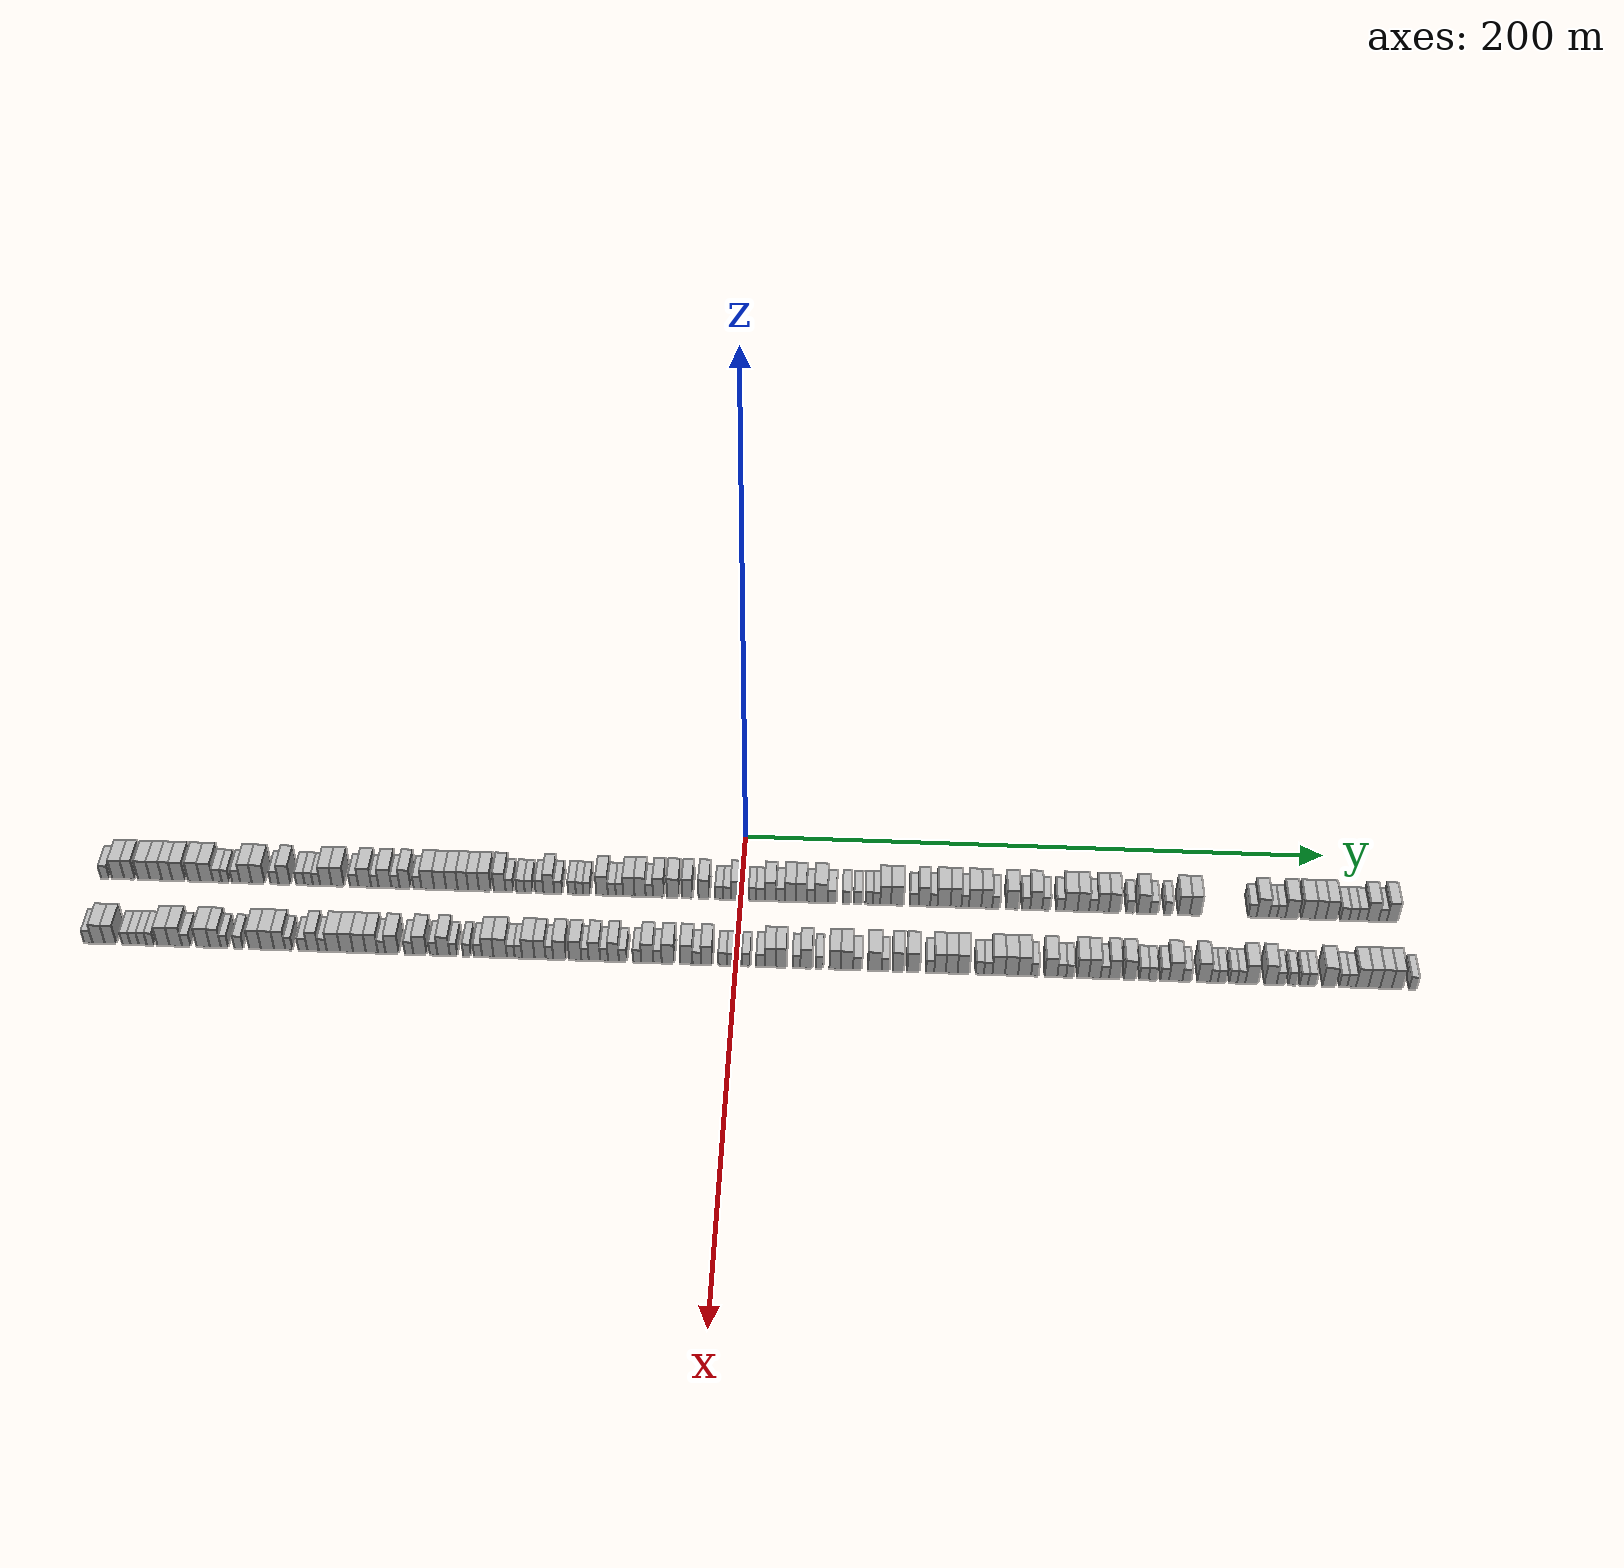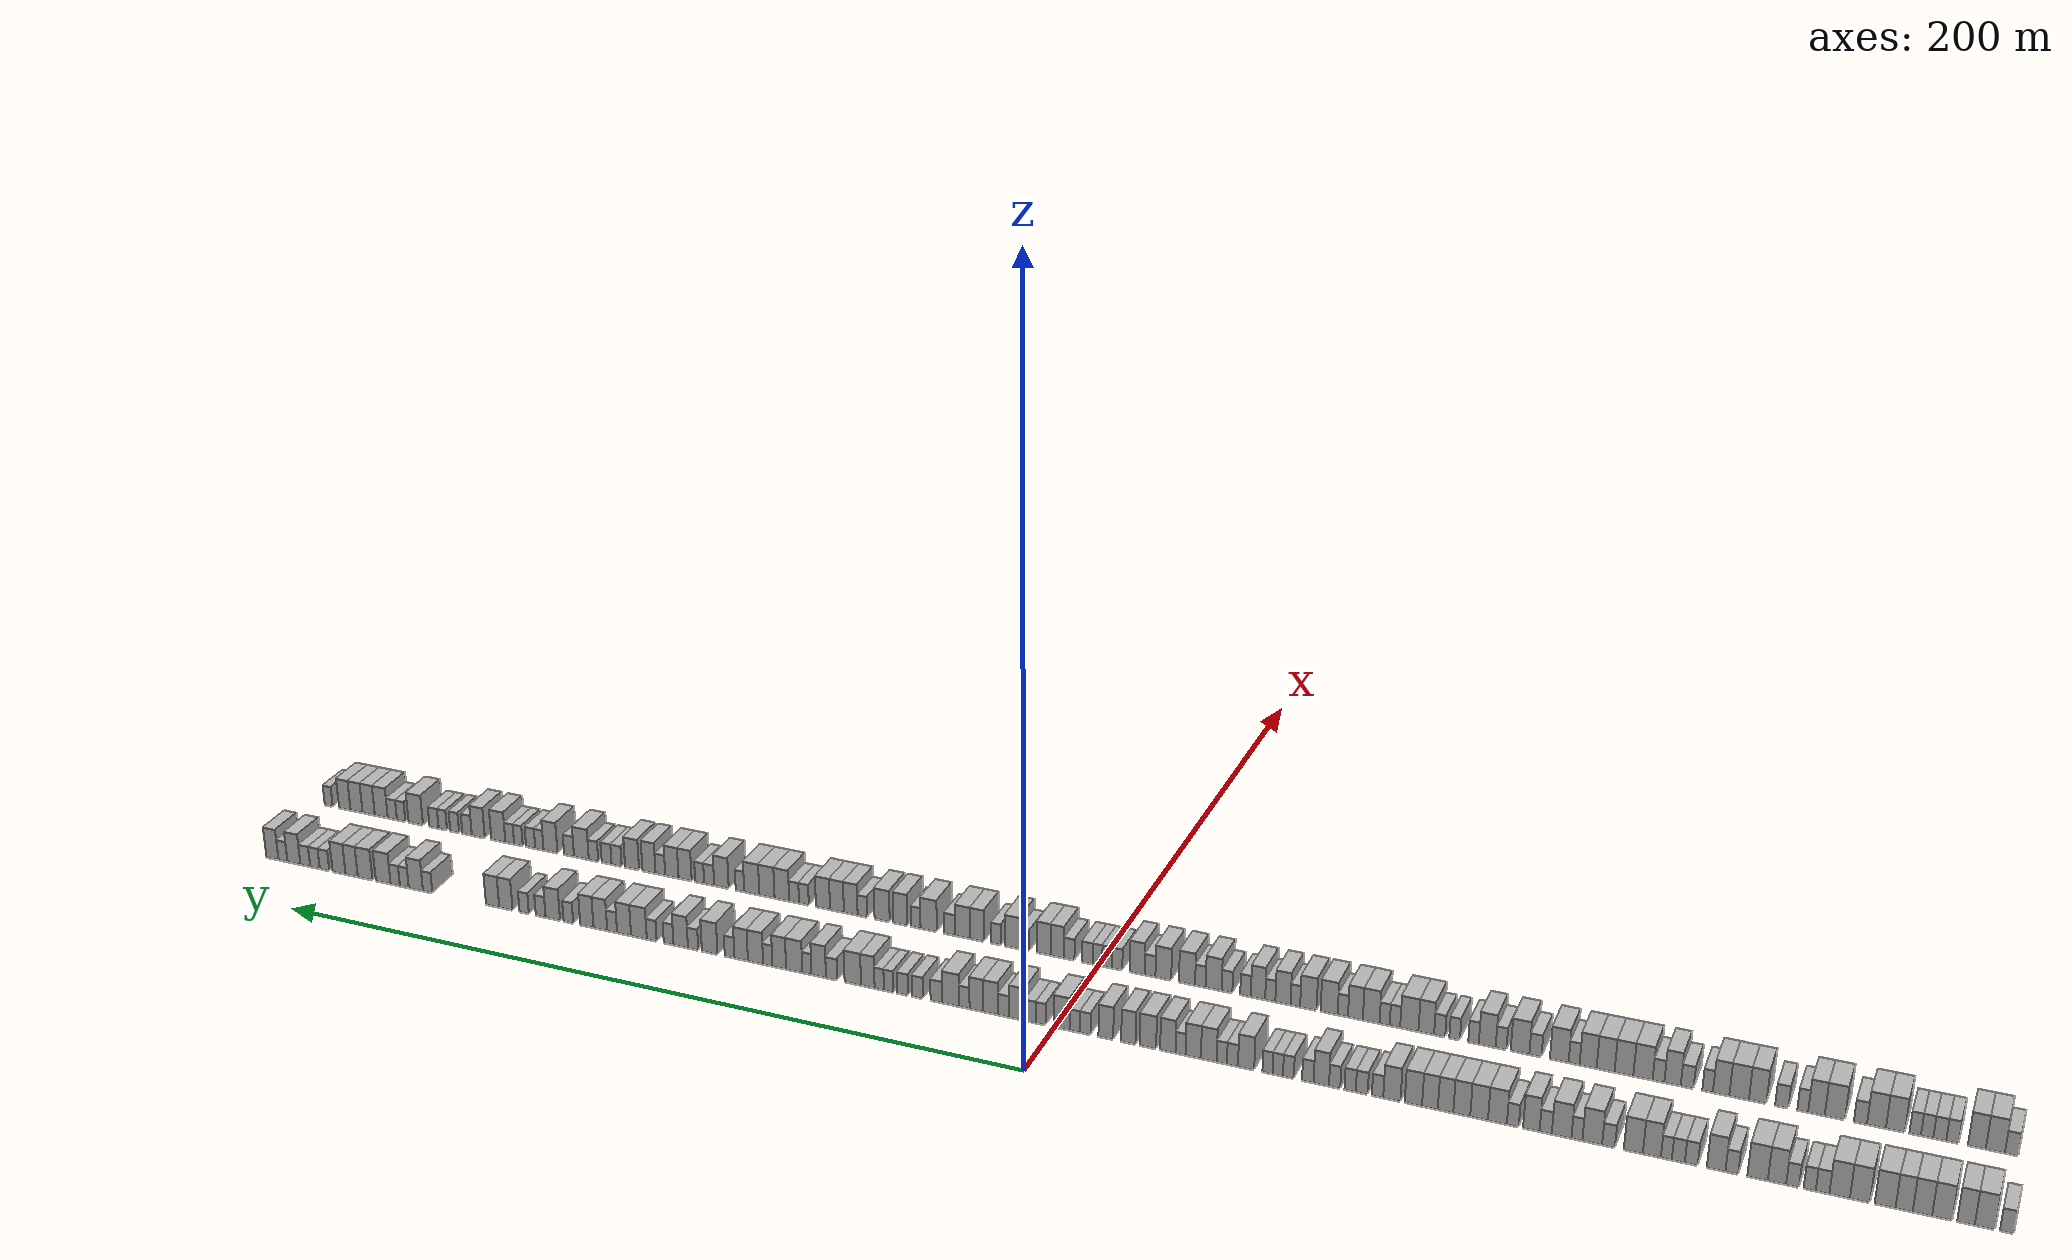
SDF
<sdf version="1.6">
 <world name="default">
  <scene>
   <sky><clouds><speed>12</speed></clouds></sky>
   <ambient>0.4 0.4 0.4 1</ambient>
   <background>0.7 0.7 0.7 1</background>
   <shadows>1</shadows>
  </scene>
  <gravity>0 0 -9.8066</gravity>
  <magnetic_field>6e-06 2.3e-05 -4.2e-05</magnetic_field>
  <physics default="0" name="default_physics" type="ode">
   <ode>
    <solver>
     <type>quick</type>
     <iters>10</iters>
     <sor>1.0</sor>
     <use_dynamic_moi_rescaling>0</use_dynamic_moi_rescaling>
    </solver>
    <constraints>
     <cfm>0</cfm>
     <erp>0.2</erp>
     <contact_max_correcting_vel>100</contact_max_correcting_vel>
     <contact_surface_layer>0.001</contact_surface_layer>
    </constraints>
   </ode>
   <max_step_size>0.004</max_step_size>
   <real_time_factor>1</real_time_factor>
   <real_time_update_rate>250</real_time_update_rate>
  </physics>
  <light name="sun" type="directional">
   <pose>0 0 10 0 0 0</pose>
   <diffuse>0.8 0.8 0.8 1</diffuse>
   <specular>0.2 0.2 0.2 1</specular>
   <attenuation>
    <range>1000</range>
    <constant>0.9</constant>
    <linear>0.01</linear>
    <quadratic>0.001</quadratic>
   </attenuation>
   <direction>-0.5 0.1 -0.9</direction>
  </light>
  <model name="building_1">
   <static>1</static>
   <pose>25.0000 -218.5460 0 0.000000 0.000000 0.000000</pose>
   <link name="link">
    <pose>0 0 3.00 0 0 0</pose>
    <collision name="collision"><geometry><box><size>10.0000 2.9079 6.0000</size></box></geometry></collision>
    <visual name="visual">
     <cast_shadows>0</cast_shadows>
     <geometry><box><size>10.0000 2.9079 6.0000</size></box></geometry>
     <material>
      <script>
       <uri>model://HANNAS_wall/materials/scripts</uri>
       <uri>model://HANNAS_wall/materials/textures</uri>
       <name>vrc/HANNAS_wall</name>
      </script>
     </material>
    </visual>
   </link>
  </model>
  <model name="building_2">
   <static>1</static>
   <pose>25.0000 -213.9712 0 0.000000 0.000000 0.000000</pose>
   <link name="link">
    <pose>0 0 4.50 0 0 0</pose>
    <collision name="collision"><geometry><box><size>10.0000 4.2417 9.0000</size></box></geometry></collision>
    <visual name="visual">
     <cast_shadows>0</cast_shadows>
     <geometry><box><size>10.0000 4.2417 9.0000</size></box></geometry>
     <material>
      <script>
       <uri>model://HANNAS_wall/materials/scripts</uri>
       <uri>model://HANNAS_wall/materials/textures</uri>
       <name>vrc/HANNAS_wall</name>
      </script>
     </material>
    </visual>
   </link>
  </model>
  <model name="building_3">
   <static>1</static>
   <pose>25.0000 -210.0111 0 0.000000 0.000000 0.000000</pose>
   <link name="link">
    <pose>0 0 4.50 0 0 0</pose>
    <collision name="collision"><geometry><box><size>10.0000 3.6786 9.0000</size></box></geometry></collision>
    <visual name="visual">
     <cast_shadows>0</cast_shadows>
     <geometry><box><size>10.0000 3.6786 9.0000</size></box></geometry>
     <material>
      <script>
       <uri>model://HANNAS_wall/materials/scripts</uri>
       <uri>model://HANNAS_wall/materials/textures</uri>
       <name>vrc/HANNAS_wall</name>
      </script>
     </material>
    </visual>
   </link>
  </model>
  <model name="building_4">
   <static>1</static>
   <pose>25.0000 -205.0438 0 0.000000 0.000000 0.000000</pose>
   <link name="link">
    <pose>0 0 4.50 0 0 0</pose>
    <collision name="collision"><geometry><box><size>10.0000 4.2560 9.0000</size></box></geometry></collision>
    <visual name="visual">
     <cast_shadows>0</cast_shadows>
     <geometry><box><size>10.0000 4.2560 9.0000</size></box></geometry>
     <material>
      <script>
       <uri>model://HANNAS_wall/materials/scripts</uri>
       <uri>model://HANNAS_wall/materials/textures</uri>
       <name>vrc/HANNAS_wall</name>
      </script>
     </material>
    </visual>
   </link>
  </model>
  <model name="building_5">
   <static>1</static>
   <pose>25.0000 -200.8795 0 0.000000 0.000000 0.000000</pose>
   <link name="link">
    <pose>0 0 4.50 0 0 0</pose>
    <collision name="collision"><geometry><box><size>10.0000 4.0725 9.0000</size></box></geometry></collision>
    <visual name="visual">
     <cast_shadows>0</cast_shadows>
     <geometry><box><size>10.0000 4.0725 9.0000</size></box></geometry>
     <material>
      <script>
       <uri>model://HANNAS_wall/materials/scripts</uri>
       <uri>model://HANNAS_wall/materials/textures</uri>
       <name>vrc/HANNAS_wall</name>
      </script>
     </material>
    </visual>
   </link>
  </model>
  <model name="building_6">
   <static>1</static>
   <pose>25.0000 -197.0260 0 0.000000 0.000000 0.000000</pose>
   <link name="link">
    <pose>0 0 4.50 0 0 0</pose>
    <collision name="collision"><geometry><box><size>10.0000 3.6344 9.0000</size></box></geometry></collision>
    <visual name="visual">
     <cast_shadows>0</cast_shadows>
     <geometry><box><size>10.0000 3.6344 9.0000</size></box></geometry>
     <material>
      <script>
       <uri>model://HANNAS_wall/materials/scripts</uri>
       <uri>model://HANNAS_wall/materials/textures</uri>
       <name>vrc/HANNAS_wall</name>
      </script>
     </material>
    </visual>
   </link>
  </model>
  <model name="building_7">
   <static>1</static>
   <pose>25.0000 -192.9910 0 0.000000 0.000000 0.000000</pose>
   <link name="link">
    <pose>0 0 4.50 0 0 0</pose>
    <collision name="collision"><geometry><box><size>10.0000 4.4356 9.0000</size></box></geometry></collision>
    <visual name="visual">
     <cast_shadows>0</cast_shadows>
     <geometry><box><size>10.0000 4.4356 9.0000</size></box></geometry>
     <material>
      <script>
       <uri>model://HANNAS_wall/materials/scripts</uri>
       <uri>model://HANNAS_wall/materials/textures</uri>
       <name>vrc/HANNAS_wall</name>
      </script>
     </material>
    </visual>
   </link>
  </model>
  <model name="building_8">
   <static>1</static>
   <pose>25.0000 -187.6323 0 0.000000 0.000000 0.000000</pose>
   <link name="link">
    <pose>0 0 4.50 0 0 0</pose>
    <collision name="collision"><geometry><box><size>10.0000 4.2819 9.0000</size></box></geometry></collision>
    <visual name="visual">
     <cast_shadows>0</cast_shadows>
     <geometry><box><size>10.0000 4.2819 9.0000</size></box></geometry>
     <material>
      <script>
       <uri>model://HANNAS_wall/materials/scripts</uri>
       <uri>model://HANNAS_wall/materials/textures</uri>
       <name>vrc/HANNAS_wall</name>
      </script>
     </material>
    </visual>
   </link>
  </model>
  <model name="building_9">
   <static>1</static>
   <pose>25.0000 -183.2862 0 0.000000 0.000000 0.000000</pose>
   <link name="link">
    <pose>0 0 4.50 0 0 0</pose>
    <collision name="collision"><geometry><box><size>10.0000 4.4103 9.0000</size></box></geometry></collision>
    <visual name="visual">
     <cast_shadows>0</cast_shadows>
     <geometry><box><size>10.0000 4.4103 9.0000</size></box></geometry>
     <material>
      <script>
       <uri>model://HANNAS_wall/materials/scripts</uri>
       <uri>model://HANNAS_wall/materials/textures</uri>
       <name>vrc/HANNAS_wall</name>
      </script>
     </material>
    </visual>
   </link>
  </model>
  <model name="building_10">
   <static>1</static>
   <pose>25.0000 -179.6199 0 0.000000 0.000000 0.000000</pose>
   <link name="link">
    <pose>0 0 3.00 0 0 0</pose>
    <collision name="collision"><geometry><box><size>10.0000 2.9221 6.0000</size></box></geometry></collision>
    <visual name="visual">
     <cast_shadows>0</cast_shadows>
     <geometry><box><size>10.0000 2.9221 6.0000</size></box></geometry>
     <material>
      <script>
       <uri>model://HANNAS_wall/materials/scripts</uri>
       <uri>model://HANNAS_wall/materials/textures</uri>
       <name>vrc/HANNAS_wall</name>
      </script>
     </material>
    </visual>
   </link>
  </model>
  <model name="building_11">
   <static>1</static>
   <pose>25.0000 -176.8499 0 0.000000 0.000000 0.000000</pose>
   <link name="link">
    <pose>0 0 3.00 0 0 0</pose>
    <collision name="collision"><geometry><box><size>10.0000 2.6181 6.0000</size></box></geometry></collision>
    <visual name="visual">
     <cast_shadows>0</cast_shadows>
     <geometry><box><size>10.0000 2.6181 6.0000</size></box></geometry>
     <material>
      <script>
       <uri>model://HANNAS_wall/materials/scripts</uri>
       <uri>model://HANNAS_wall/materials/textures</uri>
       <name>vrc/HANNAS_wall</name>
      </script>
     </material>
    </visual>
   </link>
  </model>
  <model name="building_12">
   <static>1</static>
   <pose>25.0000 -173.1496 0 0.000000 0.000000 0.000000</pose>
   <link name="link">
    <pose>0 0 3.00 0 0 0</pose>
    <collision name="collision"><geometry><box><size>10.0000 2.7825 6.0000</size></box></geometry></collision>
    <visual name="visual">
     <cast_shadows>0</cast_shadows>
     <geometry><box><size>10.0000 2.7825 6.0000</size></box></geometry>
     <material>
      <script>
       <uri>model://HANNAS_wall/materials/scripts</uri>
       <uri>model://HANNAS_wall/materials/textures</uri>
       <name>vrc/HANNAS_wall</name>
      </script>
     </material>
    </visual>
   </link>
  </model>
  <model name="building_13">
   <static>1</static>
   <pose>25.0000 -169.7729 0 0.000000 0.000000 0.000000</pose>
   <link name="link">
    <pose>0 0 4.50 0 0 0</pose>
    <collision name="collision"><geometry><box><size>10.0000 3.9707 9.0000</size></box></geometry></collision>
    <visual name="visual">
     <cast_shadows>0</cast_shadows>
     <geometry><box><size>10.0000 3.9707 9.0000</size></box></geometry>
     <material>
      <script>
       <uri>model://HANNAS_wall/materials/scripts</uri>
       <uri>model://HANNAS_wall/materials/textures</uri>
       <name>vrc/HANNAS_wall</name>
      </script>
     </material>
    </visual>
   </link>
  </model>
  <model name="building_14">
   <static>1</static>
   <pose>25.0000 -165.5477 0 0.000000 0.000000 0.000000</pose>
   <link name="link">
    <pose>0 0 4.50 0 0 0</pose>
    <collision name="collision"><geometry><box><size>10.0000 4.4798 9.0000</size></box></geometry></collision>
    <visual name="visual">
     <cast_shadows>0</cast_shadows>
     <geometry><box><size>10.0000 4.4798 9.0000</size></box></geometry>
     <material>
      <script>
       <uri>model://HANNAS_wall/materials/scripts</uri>
       <uri>model://HANNAS_wall/materials/textures</uri>
       <name>vrc/HANNAS_wall</name>
      </script>
     </material>
    </visual>
   </link>
  </model>
  <model name="building_15">
   <static>1</static>
   <pose>25.0000 -159.9158 0 0.000000 0.000000 0.000000</pose>
   <link name="link">
    <pose>0 0 3.00 0 0 0</pose>
    <collision name="collision"><geometry><box><size>10.0000 2.7840 6.0000</size></box></geometry></collision>
    <visual name="visual">
     <cast_shadows>0</cast_shadows>
     <geometry><box><size>10.0000 2.7840 6.0000</size></box></geometry>
     <material>
      <script>
       <uri>model://HANNAS_wall/materials/scripts</uri>
       <uri>model://HANNAS_wall/materials/textures</uri>
       <name>vrc/HANNAS_wall</name>
      </script>
     </material>
    </visual>
   </link>
  </model>
  <model name="building_16">
   <static>1</static>
   <pose>25.0000 -156.4676 0 0.000000 0.000000 0.000000</pose>
   <link name="link">
    <pose>0 0 4.50 0 0 0</pose>
    <collision name="collision"><geometry><box><size>10.0000 4.1124 9.0000</size></box></geometry></collision>
    <visual name="visual">
     <cast_shadows>0</cast_shadows>
     <geometry><box><size>10.0000 4.1124 9.0000</size></box></geometry>
     <material>
      <script>
       <uri>model://HANNAS_wall/materials/scripts</uri>
       <uri>model://HANNAS_wall/materials/textures</uri>
       <name>vrc/HANNAS_wall</name>
      </script>
     </material>
    </visual>
   </link>
  </model>
  <model name="building_17">
   <static>1</static>
   <pose>25.0000 -150.9805 0 0.000000 0.000000 0.000000</pose>
   <link name="link">
    <pose>0 0 3.00 0 0 0</pose>
    <collision name="collision"><geometry><box><size>10.0000 2.8616 6.0000</size></box></geometry></collision>
    <visual name="visual">
     <cast_shadows>0</cast_shadows>
     <geometry><box><size>10.0000 2.8616 6.0000</size></box></geometry>
     <material>
      <script>
       <uri>model://HANNAS_wall/materials/scripts</uri>
       <uri>model://HANNAS_wall/materials/textures</uri>
       <name>vrc/HANNAS_wall</name>
      </script>
     </material>
    </visual>
   </link>
  </model>
  <model name="building_18">
   <static>1</static>
   <pose>25.0000 -148.1120 0 0.000000 0.000000 0.000000</pose>
   <link name="link">
    <pose>0 0 3.00 0 0 0</pose>
    <collision name="collision"><geometry><box><size>10.0000 2.8755 6.0000</size></box></geometry></collision>
    <visual name="visual">
     <cast_shadows>0</cast_shadows>
     <geometry><box><size>10.0000 2.8755 6.0000</size></box></geometry>
     <material>
      <script>
       <uri>model://HANNAS_wall/materials/scripts</uri>
       <uri>model://HANNAS_wall/materials/textures</uri>
       <name>vrc/HANNAS_wall</name>
      </script>
     </material>
    </visual>
   </link>
  </model>
  <model name="building_19">
   <static>1</static>
   <pose>25.0000 -145.4479 0 0.000000 0.000000 0.000000</pose>
   <link name="link">
    <pose>0 0 3.00 0 0 0</pose>
    <collision name="collision"><geometry><box><size>10.0000 2.4528 6.0000</size></box></geometry></collision>
    <visual name="visual">
     <cast_shadows>0</cast_shadows>
     <geometry><box><size>10.0000 2.4528 6.0000</size></box></geometry>
     <material>
      <script>
       <uri>model://HANNAS_wall/materials/scripts</uri>
       <uri>model://HANNAS_wall/materials/textures</uri>
       <name>vrc/HANNAS_wall</name>
      </script>
     </material>
    </visual>
   </link>
  </model>
  <model name="building_20">
   <static>1</static>
   <pose>25.0000 -142.2186 0 0.000000 0.000000 0.000000</pose>
   <link name="link">
    <pose>0 0 4.50 0 0 0</pose>
    <collision name="collision"><geometry><box><size>10.0000 4.0057 9.0000</size></box></geometry></collision>
    <visual name="visual">
     <cast_shadows>0</cast_shadows>
     <geometry><box><size>10.0000 4.0057 9.0000</size></box></geometry>
     <material>
      <script>
       <uri>model://HANNAS_wall/materials/scripts</uri>
       <uri>model://HANNAS_wall/materials/textures</uri>
       <name>vrc/HANNAS_wall</name>
      </script>
     </material>
    </visual>
   </link>
  </model>
  <model name="building_21">
   <static>1</static>
   <pose>25.0000 -138.0832 0 0.000000 0.000000 0.000000</pose>
   <link name="link">
    <pose>0 0 4.50 0 0 0</pose>
    <collision name="collision"><geometry><box><size>10.0000 4.2652 9.0000</size></box></geometry></collision>
    <visual name="visual">
     <cast_shadows>0</cast_shadows>
     <geometry><box><size>10.0000 4.2652 9.0000</size></box></geometry>
     <material>
      <script>
       <uri>model://HANNAS_wall/materials/scripts</uri>
       <uri>model://HANNAS_wall/materials/textures</uri>
       <name>vrc/HANNAS_wall</name>
      </script>
     </material>
    </visual>
   </link>
  </model>
  <model name="building_22">
   <static>1</static>
   <pose>25.0000 -132.5046 0 0.000000 0.000000 0.000000</pose>
   <link name="link">
    <pose>0 0 3.00 0 0 0</pose>
    <collision name="collision"><geometry><box><size>10.0000 2.8920 6.0000</size></box></geometry></collision>
    <visual name="visual">
     <cast_shadows>0</cast_shadows>
     <geometry><box><size>10.0000 2.8920 6.0000</size></box></geometry>
     <material>
      <script>
       <uri>model://HANNAS_wall/materials/scripts</uri>
       <uri>model://HANNAS_wall/materials/textures</uri>
       <name>vrc/HANNAS_wall</name>
      </script>
     </material>
    </visual>
   </link>
  </model>
  <model name="building_23">
   <static>1</static>
   <pose>25.0000 -128.8323 0 0.000000 0.000000 0.000000</pose>
   <link name="link">
    <pose>0 0 4.50 0 0 0</pose>
    <collision name="collision"><geometry><box><size>10.0000 4.4527 9.0000</size></box></geometry></collision>
    <visual name="visual">
     <cast_shadows>0</cast_shadows>
     <geometry><box><size>10.0000 4.4527 9.0000</size></box></geometry>
     <material>
      <script>
       <uri>model://HANNAS_wall/materials/scripts</uri>
       <uri>model://HANNAS_wall/materials/textures</uri>
       <name>vrc/HANNAS_wall</name>
      </script>
     </material>
    </visual>
   </link>
  </model>
  <model name="building_24">
   <static>1</static>
   <pose>25.0000 -125.3593 0 0.000000 0.000000 0.000000</pose>
   <link name="link">
    <pose>0 0 3.00 0 0 0</pose>
    <collision name="collision"><geometry><box><size>10.0000 2.4932 6.0000</size></box></geometry></collision>
    <visual name="visual">
     <cast_shadows>0</cast_shadows>
     <geometry><box><size>10.0000 2.4932 6.0000</size></box></geometry>
     <material>
      <script>
       <uri>model://HANNAS_wall/materials/scripts</uri>
       <uri>model://HANNAS_wall/materials/textures</uri>
       <name>vrc/HANNAS_wall</name>
      </script>
     </material>
    </visual>
   </link>
  </model>
  <model name="building_25">
   <static>1</static>
   <pose>25.0000 -121.8784 0 0.000000 0.000000 0.000000</pose>
   <link name="link">
    <pose>0 0 4.50 0 0 0</pose>
    <collision name="collision"><geometry><box><size>10.0000 4.4687 9.0000</size></box></geometry></collision>
    <visual name="visual">
     <cast_shadows>0</cast_shadows>
     <geometry><box><size>10.0000 4.4687 9.0000</size></box></geometry>
     <material>
      <script>
       <uri>model://HANNAS_wall/materials/scripts</uri>
       <uri>model://HANNAS_wall/materials/textures</uri>
       <name>vrc/HANNAS_wall</name>
      </script>
     </material>
    </visual>
   </link>
  </model>
  <model name="building_26">
   <static>1</static>
   <pose>25.0000 -118.2513 0 0.000000 0.000000 0.000000</pose>
   <link name="link">
    <pose>0 0 3.00 0 0 0</pose>
    <collision name="collision"><geometry><box><size>10.0000 2.7856 6.0000</size></box></geometry></collision>
    <visual name="visual">
     <cast_shadows>0</cast_shadows>
     <geometry><box><size>10.0000 2.7856 6.0000</size></box></geometry>
     <material>
      <script>
       <uri>model://HANNAS_wall/materials/scripts</uri>
       <uri>model://HANNAS_wall/materials/textures</uri>
       <name>vrc/HANNAS_wall</name>
      </script>
     </material>
    </visual>
   </link>
  </model>
  <model name="building_27">
   <static>1</static>
   <pose>25.0000 -114.9687 0 0.000000 0.000000 0.000000</pose>
   <link name="link">
    <pose>0 0 4.50 0 0 0</pose>
    <collision name="collision"><geometry><box><size>10.0000 3.7795 9.0000</size></box></geometry></collision>
    <visual name="visual">
     <cast_shadows>0</cast_shadows>
     <geometry><box><size>10.0000 3.7795 9.0000</size></box></geometry>
     <material>
      <script>
       <uri>model://HANNAS_wall/materials/scripts</uri>
       <uri>model://HANNAS_wall/materials/textures</uri>
       <name>vrc/HANNAS_wall</name>
      </script>
     </material>
    </visual>
   </link>
  </model>
  <model name="building_28">
   <static>1</static>
   <pose>25.0000 -110.7197 0 0.000000 0.000000 0.000000</pose>
   <link name="link">
    <pose>0 0 3.00 0 0 0</pose>
    <collision name="collision"><geometry><box><size>10.0000 2.7185 6.0000</size></box></geometry></collision>
    <visual name="visual">
     <cast_shadows>0</cast_shadows>
     <geometry><box><size>10.0000 2.7185 6.0000</size></box></geometry>
     <material>
      <script>
       <uri>model://HANNAS_wall/materials/scripts</uri>
       <uri>model://HANNAS_wall/materials/textures</uri>
       <name>vrc/HANNAS_wall</name>
      </script>
     </material>
    </visual>
   </link>
  </model>
  <model name="building_29">
   <static>1</static>
   <pose>25.0000 -107.1760 0 0.000000 0.000000 0.000000</pose>
   <link name="link">
    <pose>0 0 4.50 0 0 0</pose>
    <collision name="collision"><geometry><box><size>10.0000 4.3689 9.0000</size></box></geometry></collision>
    <visual name="visual">
     <cast_shadows>0</cast_shadows>
     <geometry><box><size>10.0000 4.3689 9.0000</size></box></geometry>
     <material>
      <script>
       <uri>model://HANNAS_wall/materials/scripts</uri>
       <uri>model://HANNAS_wall/materials/textures</uri>
       <name>vrc/HANNAS_wall</name>
      </script>
     </material>
    </visual>
   </link>
  </model>
  <model name="building_30">
   <static>1</static>
   <pose>25.0000 -102.9325 0 0.000000 0.000000 0.000000</pose>
   <link name="link">
    <pose>0 0 4.50 0 0 0</pose>
    <collision name="collision"><geometry><box><size>10.0000 4.1180 9.0000</size></box></geometry></collision>
    <visual name="visual">
     <cast_shadows>0</cast_shadows>
     <geometry><box><size>10.0000 4.1180 9.0000</size></box></geometry>
     <material>
      <script>
       <uri>model://HANNAS_wall/materials/scripts</uri>
       <uri>model://HANNAS_wall/materials/textures</uri>
       <name>vrc/HANNAS_wall</name>
      </script>
     </material>
    </visual>
   </link>
  </model>
  <model name="building_31">
   <static>1</static>
   <pose>25.0000 -98.9012 0 0.000000 0.000000 0.000000</pose>
   <link name="link">
    <pose>0 0 4.50 0 0 0</pose>
    <collision name="collision"><geometry><box><size>10.0000 3.9447 9.0000</size></box></geometry></collision>
    <visual name="visual">
     <cast_shadows>0</cast_shadows>
     <geometry><box><size>10.0000 3.9447 9.0000</size></box></geometry>
     <material>
      <script>
       <uri>model://HANNAS_wall/materials/scripts</uri>
       <uri>model://HANNAS_wall/materials/textures</uri>
       <name>vrc/HANNAS_wall</name>
      </script>
     </material>
    </visual>
   </link>
  </model>
  <model name="building_32">
   <static>1</static>
   <pose>25.0000 -95.1221 0 0.000000 0.000000 0.000000</pose>
   <link name="link">
    <pose>0 0 4.50 0 0 0</pose>
    <collision name="collision"><geometry><box><size>10.0000 3.6135 9.0000</size></box></geometry></collision>
    <visual name="visual">
     <cast_shadows>0</cast_shadows>
     <geometry><box><size>10.0000 3.6135 9.0000</size></box></geometry>
     <material>
      <script>
       <uri>model://HANNAS_wall/materials/scripts</uri>
       <uri>model://HANNAS_wall/materials/textures</uri>
       <name>vrc/HANNAS_wall</name>
      </script>
     </material>
    </visual>
   </link>
  </model>
  <model name="building_33">
   <static>1</static>
   <pose>25.0000 -91.4711 0 0.000000 0.000000 0.000000</pose>
   <link name="link">
    <pose>0 0 4.50 0 0 0</pose>
    <collision name="collision"><geometry><box><size>10.0000 3.6884 9.0000</size></box></geometry></collision>
    <visual name="visual">
     <cast_shadows>0</cast_shadows>
     <geometry><box><size>10.0000 3.6884 9.0000</size></box></geometry>
     <material>
      <script>
       <uri>model://HANNAS_wall/materials/scripts</uri>
       <uri>model://HANNAS_wall/materials/textures</uri>
       <name>vrc/HANNAS_wall</name>
      </script>
     </material>
    </visual>
   </link>
  </model>
  <model name="building_34">
   <static>1</static>
   <pose>25.0000 -87.5866 0 0.000000 0.000000 0.000000</pose>
   <link name="link">
    <pose>0 0 4.50 0 0 0</pose>
    <collision name="collision"><geometry><box><size>10.0000 4.0806 9.0000</size></box></geometry></collision>
    <visual name="visual">
     <cast_shadows>0</cast_shadows>
     <geometry><box><size>10.0000 4.0806 9.0000</size></box></geometry>
     <material>
      <script>
       <uri>model://HANNAS_wall/materials/scripts</uri>
       <uri>model://HANNAS_wall/materials/textures</uri>
       <name>vrc/HANNAS_wall</name>
      </script>
     </material>
    </visual>
   </link>
  </model>
  <model name="building_35">
   <static>1</static>
   <pose>25.0000 -82.5160 0 0.000000 0.000000 0.000000</pose>
   <link name="link">
    <pose>0 0 4.50 0 0 0</pose>
    <collision name="collision"><geometry><box><size>10.0000 4.0606 9.0000</size></box></geometry></collision>
    <visual name="visual">
     <cast_shadows>0</cast_shadows>
     <geometry><box><size>10.0000 4.0606 9.0000</size></box></geometry>
     <material>
      <script>
       <uri>model://HANNAS_wall/materials/scripts</uri>
       <uri>model://HANNAS_wall/materials/textures</uri>
       <name>vrc/HANNAS_wall</name>
      </script>
     </material>
    </visual>
   </link>
  </model>
  <model name="building_36">
   <static>1</static>
   <pose>25.0000 -79.1424 0 0.000000 0.000000 0.000000</pose>
   <link name="link">
    <pose>0 0 3.00 0 0 0</pose>
    <collision name="collision"><geometry><box><size>10.0000 2.6865 6.0000</size></box></geometry></collision>
    <visual name="visual">
     <cast_shadows>0</cast_shadows>
     <geometry><box><size>10.0000 2.6865 6.0000</size></box></geometry>
     <material>
      <script>
       <uri>model://HANNAS_wall/materials/scripts</uri>
       <uri>model://HANNAS_wall/materials/textures</uri>
       <name>vrc/HANNAS_wall</name>
      </script>
     </material>
    </visual>
   </link>
  </model>
  <model name="building_37">
   <static>1</static>
   <pose>25.0000 -75.3794 0 0.000000 0.000000 0.000000</pose>
   <link name="link">
    <pose>0 0 3.00 0 0 0</pose>
    <collision name="collision"><geometry><box><size>10.0000 2.8395 6.0000</size></box></geometry></collision>
    <visual name="visual">
     <cast_shadows>0</cast_shadows>
     <geometry><box><size>10.0000 2.8395 6.0000</size></box></geometry>
     <material>
      <script>
       <uri>model://HANNAS_wall/materials/scripts</uri>
       <uri>model://HANNAS_wall/materials/textures</uri>
       <name>vrc/HANNAS_wall</name>
      </script>
     </material>
    </visual>
   </link>
  </model>
  <model name="building_38">
   <static>1</static>
   <pose>25.0000 -72.6136 0 0.000000 0.000000 0.000000</pose>
   <link name="link">
    <pose>0 0 3.00 0 0 0</pose>
    <collision name="collision"><geometry><box><size>10.0000 2.6922 6.0000</size></box></geometry></collision>
    <visual name="visual">
     <cast_shadows>0</cast_shadows>
     <geometry><box><size>10.0000 2.6922 6.0000</size></box></geometry>
     <material>
      <script>
       <uri>model://HANNAS_wall/materials/scripts</uri>
       <uri>model://HANNAS_wall/materials/textures</uri>
       <name>vrc/HANNAS_wall</name>
      </script>
     </material>
    </visual>
   </link>
  </model>
  <model name="building_39">
   <static>1</static>
   <pose>25.0000 -68.9163 0 0.000000 0.000000 0.000000</pose>
   <link name="link">
    <pose>0 0 3.00 0 0 0</pose>
    <collision name="collision"><geometry><box><size>10.0000 2.7024 6.0000</size></box></geometry></collision>
    <visual name="visual">
     <cast_shadows>0</cast_shadows>
     <geometry><box><size>10.0000 2.7024 6.0000</size></box></geometry>
     <material>
      <script>
       <uri>model://HANNAS_wall/materials/scripts</uri>
       <uri>model://HANNAS_wall/materials/textures</uri>
       <name>vrc/HANNAS_wall</name>
      </script>
     </material>
    </visual>
   </link>
  </model>
  <model name="building_40">
   <static>1</static>
   <pose>25.0000 -65.7178 0 0.000000 0.000000 0.000000</pose>
   <link name="link">
    <pose>0 0 4.50 0 0 0</pose>
    <collision name="collision"><geometry><box><size>10.0000 3.6947 9.0000</size></box></geometry></collision>
    <visual name="visual">
     <cast_shadows>0</cast_shadows>
     <geometry><box><size>10.0000 3.6947 9.0000</size></box></geometry>
     <material>
      <script>
       <uri>model://HANNAS_wall/materials/scripts</uri>
       <uri>model://HANNAS_wall/materials/textures</uri>
       <name>vrc/HANNAS_wall</name>
      </script>
     </material>
    </visual>
   </link>
  </model>
  <model name="building_41">
   <static>1</static>
   <pose>25.0000 -62.4882 0 0.000000 0.000000 0.000000</pose>
   <link name="link">
    <pose>0 0 3.00 0 0 0</pose>
    <collision name="collision"><geometry><box><size>10.0000 2.7646 6.0000</size></box></geometry></collision>
    <visual name="visual">
     <cast_shadows>0</cast_shadows>
     <geometry><box><size>10.0000 2.7646 6.0000</size></box></geometry>
     <material>
      <script>
       <uri>model://HANNAS_wall/materials/scripts</uri>
       <uri>model://HANNAS_wall/materials/textures</uri>
       <name>vrc/HANNAS_wall</name>
      </script>
     </material>
    </visual>
   </link>
  </model>
  <model name="building_42">
   <static>1</static>
   <pose>25.0000 -57.7956 0 0.000000 0.000000 0.000000</pose>
   <link name="link">
    <pose>0 0 3.00 0 0 0</pose>
    <collision name="collision"><geometry><box><size>10.0000 2.6207 6.0000</size></box></geometry></collision>
    <visual name="visual">
     <cast_shadows>0</cast_shadows>
     <geometry><box><size>10.0000 2.6207 6.0000</size></box></geometry>
     <material>
      <script>
       <uri>model://HANNAS_wall/materials/scripts</uri>
       <uri>model://HANNAS_wall/materials/textures</uri>
       <name>vrc/HANNAS_wall</name>
      </script>
     </material>
    </visual>
   </link>
  </model>
  <model name="building_43">
   <static>1</static>
   <pose>25.0000 -55.2226 0 0.000000 0.000000 0.000000</pose>
   <link name="link">
    <pose>0 0 3.00 0 0 0</pose>
    <collision name="collision"><geometry><box><size>10.0000 2.5253 6.0000</size></box></geometry></collision>
    <visual name="visual">
     <cast_shadows>0</cast_shadows>
     <geometry><box><size>10.0000 2.5253 6.0000</size></box></geometry>
     <material>
      <script>
       <uri>model://HANNAS_wall/materials/scripts</uri>
       <uri>model://HANNAS_wall/materials/textures</uri>
       <name>vrc/HANNAS_wall</name>
      </script>
     </material>
    </visual>
   </link>
  </model>
  <model name="building_44">
   <static>1</static>
   <pose>25.0000 -52.7311 0 0.000000 0.000000 0.000000</pose>
   <link name="link">
    <pose>0 0 3.00 0 0 0</pose>
    <collision name="collision"><geometry><box><size>10.0000 2.4576 6.0000</size></box></geometry></collision>
    <visual name="visual">
     <cast_shadows>0</cast_shadows>
     <geometry><box><size>10.0000 2.4576 6.0000</size></box></geometry>
     <material>
      <script>
       <uri>model://HANNAS_wall/materials/scripts</uri>
       <uri>model://HANNAS_wall/materials/textures</uri>
       <name>vrc/HANNAS_wall</name>
      </script>
     </material>
    </visual>
   </link>
  </model>
  <model name="building_45">
   <static>1</static>
   <pose>25.0000 -47.5219 0 0.000000 0.000000 0.000000</pose>
   <link name="link">
    <pose>0 0 4.50 0 0 0</pose>
    <collision name="collision"><geometry><box><size>10.0000 3.9609 9.0000</size></box></geometry></collision>
    <visual name="visual">
     <cast_shadows>0</cast_shadows>
     <geometry><box><size>10.0000 3.9609 9.0000</size></box></geometry>
     <material>
      <script>
       <uri>model://HANNAS_wall/materials/scripts</uri>
       <uri>model://HANNAS_wall/materials/textures</uri>
       <name>vrc/HANNAS_wall</name>
      </script>
     </material>
    </visual>
   </link>
  </model>
  <model name="building_46">
   <static>1</static>
   <pose>25.0000 -44.1928 0 0.000000 0.000000 0.000000</pose>
   <link name="link">
    <pose>0 0 3.00 0 0 0</pose>
    <collision name="collision"><geometry><box><size>10.0000 2.6975 6.0000</size></box></geometry></collision>
    <visual name="visual">
     <cast_shadows>0</cast_shadows>
     <geometry><box><size>10.0000 2.6975 6.0000</size></box></geometry>
     <material>
      <script>
       <uri>model://HANNAS_wall/materials/scripts</uri>
       <uri>model://HANNAS_wall/materials/textures</uri>
       <name>vrc/HANNAS_wall</name>
      </script>
     </material>
    </visual>
   </link>
  </model>
  <model name="building_47">
   <static>1</static>
   <pose>25.0000 -41.5849 0 0.000000 0.000000 0.000000</pose>
   <link name="link">
    <pose>0 0 3.00 0 0 0</pose>
    <collision name="collision"><geometry><box><size>10.0000 2.5183 6.0000</size></box></geometry></collision>
    <visual name="visual">
     <cast_shadows>0</cast_shadows>
     <geometry><box><size>10.0000 2.5183 6.0000</size></box></geometry>
     <material>
      <script>
       <uri>model://HANNAS_wall/materials/scripts</uri>
       <uri>model://HANNAS_wall/materials/textures</uri>
       <name>vrc/HANNAS_wall</name>
      </script>
     </material>
    </visual>
   </link>
  </model>
  <model name="building_48">
   <static>1</static>
   <pose>25.0000 -38.3854 0 0.000000 0.000000 0.000000</pose>
   <link name="link">
    <pose>0 0 4.50 0 0 0</pose>
    <collision name="collision"><geometry><box><size>10.0000 3.8806 9.0000</size></box></geometry></collision>
    <visual name="visual">
     <cast_shadows>0</cast_shadows>
     <geometry><box><size>10.0000 3.8806 9.0000</size></box></geometry>
     <material>
      <script>
       <uri>model://HANNAS_wall/materials/scripts</uri>
       <uri>model://HANNAS_wall/materials/textures</uri>
       <name>vrc/HANNAS_wall</name>
      </script>
     </material>
    </visual>
   </link>
  </model>
  <model name="building_49">
   <static>1</static>
   <pose>25.0000 -34.5562 0 0.000000 0.000000 0.000000</pose>
   <link name="link">
    <pose>0 0 4.50 0 0 0</pose>
    <collision name="collision"><geometry><box><size>10.0000 3.7779 9.0000</size></box></geometry></collision>
    <visual name="visual">
     <cast_shadows>0</cast_shadows>
     <geometry><box><size>10.0000 3.7779 9.0000</size></box></geometry>
     <material>
      <script>
       <uri>model://HANNAS_wall/materials/scripts</uri>
       <uri>model://HANNAS_wall/materials/textures</uri>
       <name>vrc/HANNAS_wall</name>
      </script>
     </material>
    </visual>
   </link>
  </model>
  <model name="building_50">
   <static>1</static>
   <pose>25.0000 -31.4107 0 0.000000 0.000000 0.000000</pose>
   <link name="link">
    <pose>0 0 3.00 0 0 0</pose>
    <collision name="collision"><geometry><box><size>10.0000 2.5132 6.0000</size></box></geometry></collision>
    <visual name="visual">
     <cast_shadows>0</cast_shadows>
     <geometry><box><size>10.0000 2.5132 6.0000</size></box></geometry>
     <material>
      <script>
       <uri>model://HANNAS_wall/materials/scripts</uri>
       <uri>model://HANNAS_wall/materials/textures</uri>
       <name>vrc/HANNAS_wall</name>
      </script>
     </material>
    </visual>
   </link>
  </model>
  <model name="building_51">
   <static>1</static>
   <pose>25.0000 -28.2567 0 0.000000 0.000000 0.000000</pose>
   <link name="link">
    <pose>0 0 4.50 0 0 0</pose>
    <collision name="collision"><geometry><box><size>10.0000 3.7947 9.0000</size></box></geometry></collision>
    <visual name="visual">
     <cast_shadows>0</cast_shadows>
     <geometry><box><size>10.0000 3.7947 9.0000</size></box></geometry>
     <material>
      <script>
       <uri>model://HANNAS_wall/materials/scripts</uri>
       <uri>model://HANNAS_wall/materials/textures</uri>
       <name>vrc/HANNAS_wall</name>
      </script>
     </material>
    </visual>
   </link>
  </model>
  <model name="building_52">
   <static>1</static>
   <pose>25.0000 -23.2993 0 0.000000 0.000000 0.000000</pose>
   <link name="link">
    <pose>0 0 4.50 0 0 0</pose>
    <collision name="collision"><geometry><box><size>10.0000 4.1200 9.0000</size></box></geometry></collision>
    <visual name="visual">
     <cast_shadows>0</cast_shadows>
     <geometry><box><size>10.0000 4.1200 9.0000</size></box></geometry>
     <material>
      <script>
       <uri>model://HANNAS_wall/materials/scripts</uri>
       <uri>model://HANNAS_wall/materials/textures</uri>
       <name>vrc/HANNAS_wall</name>
      </script>
     </material>
    </visual>
   </link>
  </model>
  <model name="building_53">
   <static>1</static>
   <pose>25.0000 -18.4316 0 0.000000 0.000000 0.000000</pose>
   <link name="link">
    <pose>0 0 4.50 0 0 0</pose>
    <collision name="collision"><geometry><box><size>10.0000 3.6155 9.0000</size></box></geometry></collision>
    <visual name="visual">
     <cast_shadows>0</cast_shadows>
     <geometry><box><size>10.0000 3.6155 9.0000</size></box></geometry>
     <material>
      <script>
       <uri>model://HANNAS_wall/materials/scripts</uri>
       <uri>model://HANNAS_wall/materials/textures</uri>
       <name>vrc/HANNAS_wall</name>
      </script>
     </material>
    </visual>
   </link>
  </model>
  <model name="building_54">
   <static>1</static>
   <pose>25.0000 -12.7551 0 0.000000 0.000000 0.000000</pose>
   <link name="link">
    <pose>0 0 4.50 0 0 0</pose>
    <collision name="collision"><geometry><box><size>10.0000 3.7376 9.0000</size></box></geometry></collision>
    <visual name="visual">
     <cast_shadows>0</cast_shadows>
     <geometry><box><size>10.0000 3.7376 9.0000</size></box></geometry>
     <material>
      <script>
       <uri>model://HANNAS_wall/materials/scripts</uri>
       <uri>model://HANNAS_wall/materials/textures</uri>
       <name>vrc/HANNAS_wall</name>
      </script>
     </material>
    </visual>
   </link>
  </model>
  <model name="building_55">
   <static>1</static>
   <pose>25.0000 -7.5630 0 0.000000 0.000000 0.000000</pose>
   <link name="link">
    <pose>0 0 3.00 0 0 0</pose>
    <collision name="collision"><geometry><box><size>10.0000 2.6465 6.0000</size></box></geometry></collision>
    <visual name="visual">
     <cast_shadows>0</cast_shadows>
     <geometry><box><size>10.0000 2.6465 6.0000</size></box></geometry>
     <material>
      <script>
       <uri>model://HANNAS_wall/materials/scripts</uri>
       <uri>model://HANNAS_wall/materials/textures</uri>
       <name>vrc/HANNAS_wall</name>
      </script>
     </material>
    </visual>
   </link>
  </model>
  <model name="building_56">
   <static>1</static>
   <pose>25.0000 -4.9420 0 0.000000 0.000000 0.000000</pose>
   <link name="link">
    <pose>0 0 3.00 0 0 0</pose>
    <collision name="collision"><geometry><box><size>10.0000 2.5955 6.0000</size></box></geometry></collision>
    <visual name="visual">
     <cast_shadows>0</cast_shadows>
     <geometry><box><size>10.0000 2.5955 6.0000</size></box></geometry>
     <material>
      <script>
       <uri>model://HANNAS_wall/materials/scripts</uri>
       <uri>model://HANNAS_wall/materials/textures</uri>
       <name>vrc/HANNAS_wall</name>
      </script>
     </material>
    </visual>
   </link>
  </model>
  <model name="building_57">
   <static>1</static>
   <pose>25.0000 -1.5635 0 0.000000 0.000000 0.000000</pose>
   <link name="link">
    <pose>0 0 4.50 0 0 0</pose>
    <collision name="collision"><geometry><box><size>10.0000 4.1615 9.0000</size></box></geometry></collision>
    <visual name="visual">
     <cast_shadows>0</cast_shadows>
     <geometry><box><size>10.0000 4.1615 9.0000</size></box></geometry>
     <material>
      <script>
       <uri>model://HANNAS_wall/materials/scripts</uri>
       <uri>model://HANNAS_wall/materials/textures</uri>
       <name>vrc/HANNAS_wall</name>
      </script>
     </material>
    </visual>
   </link>
  </model>
  <model name="building_58">
   <static>1</static>
   <pose>25.0000 3.7501 0 0.000000 0.000000 0.000000</pose>
   <link name="link">
    <pose>0 0 3.00 0 0 0</pose>
    <collision name="collision"><geometry><box><size>10.0000 2.4657 6.0000</size></box></geometry></collision>
    <visual name="visual">
     <cast_shadows>0</cast_shadows>
     <geometry><box><size>10.0000 2.4657 6.0000</size></box></geometry>
     <material>
      <script>
       <uri>model://HANNAS_wall/materials/scripts</uri>
       <uri>model://HANNAS_wall/materials/textures</uri>
       <name>vrc/HANNAS_wall</name>
      </script>
     </material>
    </visual>
   </link>
  </model>
  <model name="building_59">
   <static>1</static>
   <pose>25.0000 6.4249 0 0.000000 0.000000 0.000000</pose>
   <link name="link">
    <pose>0 0 3.00 0 0 0</pose>
    <collision name="collision"><geometry><box><size>10.0000 2.8840 6.0000</size></box></geometry></collision>
    <visual name="visual">
     <cast_shadows>0</cast_shadows>
     <geometry><box><size>10.0000 2.8840 6.0000</size></box></geometry>
     <material>
      <script>
       <uri>model://HANNAS_wall/materials/scripts</uri>
       <uri>model://HANNAS_wall/materials/textures</uri>
       <name>vrc/HANNAS_wall</name>
      </script>
     </material>
    </visual>
   </link>
  </model>
  <model name="building_60">
   <static>1</static>
   <pose>25.0000 9.8533 0 0.000000 0.000000 0.000000</pose>
   <link name="link">
    <pose>0 0 4.50 0 0 0</pose>
    <collision name="collision"><geometry><box><size>10.0000 3.9727 9.0000</size></box></geometry></collision>
    <visual name="visual">
     <cast_shadows>0</cast_shadows>
     <geometry><box><size>10.0000 3.9727 9.0000</size></box></geometry>
     <material>
      <script>
       <uri>model://HANNAS_wall/materials/scripts</uri>
       <uri>model://HANNAS_wall/materials/textures</uri>
       <name>vrc/HANNAS_wall</name>
      </script>
     </material>
    </visual>
   </link>
  </model>
  <model name="building_61">
   <static>1</static>
   <pose>25.0000 13.3222 0 0.000000 0.000000 0.000000</pose>
   <link name="link">
    <pose>0 0 3.00 0 0 0</pose>
    <collision name="collision"><geometry><box><size>10.0000 2.9652 6.0000</size></box></geometry></collision>
    <visual name="visual">
     <cast_shadows>0</cast_shadows>
     <geometry><box><size>10.0000 2.9652 6.0000</size></box></geometry>
     <material>
      <script>
       <uri>model://HANNAS_wall/materials/scripts</uri>
       <uri>model://HANNAS_wall/materials/textures</uri>
       <name>vrc/HANNAS_wall</name>
      </script>
     </material>
    </visual>
   </link>
  </model>
  <model name="building_62">
   <static>1</static>
   <pose>25.0000 16.6622 0 0.000000 0.000000 0.000000</pose>
   <link name="link">
    <pose>0 0 4.50 0 0 0</pose>
    <collision name="collision"><geometry><box><size>10.0000 3.7147 9.0000</size></box></geometry></collision>
    <visual name="visual">
     <cast_shadows>0</cast_shadows>
     <geometry><box><size>10.0000 3.7147 9.0000</size></box></geometry>
     <material>
      <script>
       <uri>model://HANNAS_wall/materials/scripts</uri>
       <uri>model://HANNAS_wall/materials/textures</uri>
       <name>vrc/HANNAS_wall</name>
      </script>
     </material>
    </visual>
   </link>
  </model>
  <model name="building_63">
   <static>1</static>
   <pose>25.0000 20.3281 0 0.000000 0.000000 0.000000</pose>
   <link name="link">
    <pose>0 0 4.50 0 0 0</pose>
    <collision name="collision"><geometry><box><size>10.0000 3.6170 9.0000</size></box></geometry></collision>
    <visual name="visual">
     <cast_shadows>0</cast_shadows>
     <geometry><box><size>10.0000 3.6170 9.0000</size></box></geometry>
     <material>
      <script>
       <uri>model://HANNAS_wall/materials/scripts</uri>
       <uri>model://HANNAS_wall/materials/textures</uri>
       <name>vrc/HANNAS_wall</name>
      </script>
     </material>
    </visual>
   </link>
  </model>
  <model name="building_64">
   <static>1</static>
   <pose>25.0000 23.4946 0 0.000000 0.000000 0.000000</pose>
   <link name="link">
    <pose>0 0 3.00 0 0 0</pose>
    <collision name="collision"><geometry><box><size>10.0000 2.7159 6.0000</size></box></geometry></collision>
    <visual name="visual">
     <cast_shadows>0</cast_shadows>
     <geometry><box><size>10.0000 2.7159 6.0000</size></box></geometry>
     <material>
      <script>
       <uri>model://HANNAS_wall/materials/scripts</uri>
       <uri>model://HANNAS_wall/materials/textures</uri>
       <name>vrc/HANNAS_wall</name>
      </script>
     </material>
    </visual>
   </link>
  </model>
  <model name="building_65">
   <static>1</static>
   <pose>25.0000 27.0919 0 0.000000 0.000000 0.000000</pose>
   <link name="link">
    <pose>0 0 4.50 0 0 0</pose>
    <collision name="collision"><geometry><box><size>10.0000 4.4787 9.0000</size></box></geometry></collision>
    <visual name="visual">
     <cast_shadows>0</cast_shadows>
     <geometry><box><size>10.0000 4.4787 9.0000</size></box></geometry>
     <material>
      <script>
       <uri>model://HANNAS_wall/materials/scripts</uri>
       <uri>model://HANNAS_wall/materials/textures</uri>
       <name>vrc/HANNAS_wall</name>
      </script>
     </material>
    </visual>
   </link>
  </model>
  <model name="building_66">
   <static>1</static>
   <pose>25.0000 30.8245 0 0.000000 0.000000 0.000000</pose>
   <link name="link">
    <pose>0 0 3.00 0 0 0</pose>
    <collision name="collision"><geometry><box><size>10.0000 2.9864 6.0000</size></box></geometry></collision>
    <visual name="visual">
     <cast_shadows>0</cast_shadows>
     <geometry><box><size>10.0000 2.9864 6.0000</size></box></geometry>
     <material>
      <script>
       <uri>model://HANNAS_wall/materials/scripts</uri>
       <uri>model://HANNAS_wall/materials/textures</uri>
       <name>vrc/HANNAS_wall</name>
      </script>
     </material>
    </visual>
   </link>
  </model>
  <model name="building_67">
   <static>1</static>
   <pose>25.0000 35.7682 0 0.000000 0.000000 0.000000</pose>
   <link name="link">
    <pose>0 0 3.00 0 0 0</pose>
    <collision name="collision"><geometry><box><size>10.0000 2.9010 6.0000</size></box></geometry></collision>
    <visual name="visual">
     <cast_shadows>0</cast_shadows>
     <geometry><box><size>10.0000 2.9010 6.0000</size></box></geometry>
     <material>
      <script>
       <uri>model://HANNAS_wall/materials/scripts</uri>
       <uri>model://HANNAS_wall/materials/textures</uri>
       <name>vrc/HANNAS_wall</name>
      </script>
     </material>
    </visual>
   </link>
  </model>
  <model name="building_68">
   <static>1</static>
   <pose>25.0000 39.6555 0 0.000000 0.000000 0.000000</pose>
   <link name="link">
    <pose>0 0 3.00 0 0 0</pose>
    <collision name="collision"><geometry><box><size>10.0000 2.8736 6.0000</size></box></geometry></collision>
    <visual name="visual">
     <cast_shadows>0</cast_shadows>
     <geometry><box><size>10.0000 2.8736 6.0000</size></box></geometry>
     <material>
      <script>
       <uri>model://HANNAS_wall/materials/scripts</uri>
       <uri>model://HANNAS_wall/materials/textures</uri>
       <name>vrc/HANNAS_wall</name>
      </script>
     </material>
    </visual>
   </link>
  </model>
  <model name="building_69">
   <static>1</static>
   <pose>25.0000 43.3663 0 0.000000 0.000000 0.000000</pose>
   <link name="link">
    <pose>0 0 3.00 0 0 0</pose>
    <collision name="collision"><geometry><box><size>10.0000 2.5479 6.0000</size></box></geometry></collision>
    <visual name="visual">
     <cast_shadows>0</cast_shadows>
     <geometry><box><size>10.0000 2.5479 6.0000</size></box></geometry>
     <material>
      <script>
       <uri>model://HANNAS_wall/materials/scripts</uri>
       <uri>model://HANNAS_wall/materials/textures</uri>
       <name>vrc/HANNAS_wall</name>
      </script>
     </material>
    </visual>
   </link>
  </model>
  <model name="building_70">
   <static>1</static>
   <pose>25.0000 45.8684 0 0.000000 0.000000 0.000000</pose>
   <link name="link">
    <pose>0 0 3.00 0 0 0</pose>
    <collision name="collision"><geometry><box><size>10.0000 2.4564 6.0000</size></box></geometry></collision>
    <visual name="visual">
     <cast_shadows>0</cast_shadows>
     <geometry><box><size>10.0000 2.4564 6.0000</size></box></geometry>
     <material>
      <script>
       <uri>model://HANNAS_wall/materials/scripts</uri>
       <uri>model://HANNAS_wall/materials/textures</uri>
       <name>vrc/HANNAS_wall</name>
      </script>
     </material>
    </visual>
   </link>
  </model>
  <model name="building_71">
   <static>1</static>
   <pose>25.0000 48.9120 0 0.000000 0.000000 0.000000</pose>
   <link name="link">
    <pose>0 0 4.50 0 0 0</pose>
    <collision name="collision"><geometry><box><size>10.0000 3.6307 9.0000</size></box></geometry></collision>
    <visual name="visual">
     <cast_shadows>0</cast_shadows>
     <geometry><box><size>10.0000 3.6307 9.0000</size></box></geometry>
     <material>
      <script>
       <uri>model://HANNAS_wall/materials/scripts</uri>
       <uri>model://HANNAS_wall/materials/textures</uri>
       <name>vrc/HANNAS_wall</name>
      </script>
     </material>
    </visual>
   </link>
  </model>
  <model name="building_72">
   <static>1</static>
   <pose>25.0000 52.9162 0 0.000000 0.000000 0.000000</pose>
   <link name="link">
    <pose>0 0 4.50 0 0 0</pose>
    <collision name="collision"><geometry><box><size>10.0000 4.3778 9.0000</size></box></geometry></collision>
    <visual name="visual">
     <cast_shadows>0</cast_shadows>
     <geometry><box><size>10.0000 4.3778 9.0000</size></box></geometry>
     <material>
      <script>
       <uri>model://HANNAS_wall/materials/scripts</uri>
       <uri>model://HANNAS_wall/materials/textures</uri>
       <name>vrc/HANNAS_wall</name>
      </script>
     </material>
    </visual>
   </link>
  </model>
  <model name="building_73">
   <static>1</static>
   <pose>25.0000 58.6040 0 0.000000 0.000000 0.000000</pose>
   <link name="link">
    <pose>0 0 3.00 0 0 0</pose>
    <collision name="collision"><geometry><box><size>10.0000 2.9978 6.0000</size></box></geometry></collision>
    <visual name="visual">
     <cast_shadows>0</cast_shadows>
     <geometry><box><size>10.0000 2.9978 6.0000</size></box></geometry>
     <material>
      <script>
       <uri>model://HANNAS_wall/materials/scripts</uri>
       <uri>model://HANNAS_wall/materials/textures</uri>
       <name>vrc/HANNAS_wall</name>
      </script>
     </material>
    </visual>
   </link>
  </model>
  <model name="building_74">
   <static>1</static>
   <pose>25.0000 62.0580 0 0.000000 0.000000 0.000000</pose>
   <link name="link">
    <pose>0 0 4.50 0 0 0</pose>
    <collision name="collision"><geometry><box><size>10.0000 3.9103 9.0000</size></box></geometry></collision>
    <visual name="visual">
     <cast_shadows>0</cast_shadows>
     <geometry><box><size>10.0000 3.9103 9.0000</size></box></geometry>
     <material>
      <script>
       <uri>model://HANNAS_wall/materials/scripts</uri>
       <uri>model://HANNAS_wall/materials/textures</uri>
       <name>vrc/HANNAS_wall</name>
      </script>
     </material>
    </visual>
   </link>
  </model>
  <model name="building_75">
   <static>1</static>
   <pose>25.0000 65.2434 0 0.000000 0.000000 0.000000</pose>
   <link name="link">
    <pose>0 0 3.00 0 0 0</pose>
    <collision name="collision"><geometry><box><size>10.0000 2.4604 6.0000</size></box></geometry></collision>
    <visual name="visual">
     <cast_shadows>0</cast_shadows>
     <geometry><box><size>10.0000 2.4604 6.0000</size></box></geometry>
     <material>
      <script>
       <uri>model://HANNAS_wall/materials/scripts</uri>
       <uri>model://HANNAS_wall/materials/textures</uri>
       <name>vrc/HANNAS_wall</name>
      </script>
     </material>
    </visual>
   </link>
  </model>
  <model name="building_76">
   <static>1</static>
   <pose>25.0000 68.6689 0 0.000000 0.000000 0.000000</pose>
   <link name="link">
    <pose>0 0 4.50 0 0 0</pose>
    <collision name="collision"><geometry><box><size>10.0000 4.3907 9.0000</size></box></geometry></collision>
    <visual name="visual">
     <cast_shadows>0</cast_shadows>
     <geometry><box><size>10.0000 4.3907 9.0000</size></box></geometry>
     <material>
      <script>
       <uri>model://HANNAS_wall/materials/scripts</uri>
       <uri>model://HANNAS_wall/materials/textures</uri>
       <name>vrc/HANNAS_wall</name>
      </script>
     </material>
    </visual>
   </link>
  </model>
  <model name="building_77">
   <static>1</static>
   <pose>25.0000 72.7252 0 0.000000 0.000000 0.000000</pose>
   <link name="link">
    <pose>0 0 4.50 0 0 0</pose>
    <collision name="collision"><geometry><box><size>10.0000 3.7220 9.0000</size></box></geometry></collision>
    <visual name="visual">
     <cast_shadows>0</cast_shadows>
     <geometry><box><size>10.0000 3.7220 9.0000</size></box></geometry>
     <material>
      <script>
       <uri>model://HANNAS_wall/materials/scripts</uri>
       <uri>model://HANNAS_wall/materials/textures</uri>
       <name>vrc/HANNAS_wall</name>
      </script>
     </material>
    </visual>
   </link>
  </model>
  <model name="building_78">
   <static>1</static>
   <pose>25.0000 75.8504 0 0.000000 0.000000 0.000000</pose>
   <link name="link">
    <pose>0 0 3.00 0 0 0</pose>
    <collision name="collision"><geometry><box><size>10.0000 2.5285 6.0000</size></box></geometry></collision>
    <visual name="visual">
     <cast_shadows>0</cast_shadows>
     <geometry><box><size>10.0000 2.5285 6.0000</size></box></geometry>
     <material>
      <script>
       <uri>model://HANNAS_wall/materials/scripts</uri>
       <uri>model://HANNAS_wall/materials/textures</uri>
       <name>vrc/HANNAS_wall</name>
      </script>
     </material>
    </visual>
   </link>
  </model>
  <model name="building_79">
   <static>1</static>
   <pose>25.0000 79.2033 0 0.000000 0.000000 0.000000</pose>
   <link name="link">
    <pose>0 0 4.50 0 0 0</pose>
    <collision name="collision"><geometry><box><size>10.0000 4.1771 9.0000</size></box></geometry></collision>
    <visual name="visual">
     <cast_shadows>0</cast_shadows>
     <geometry><box><size>10.0000 4.1771 9.0000</size></box></geometry>
     <material>
      <script>
       <uri>model://HANNAS_wall/materials/scripts</uri>
       <uri>model://HANNAS_wall/materials/textures</uri>
       <name>vrc/HANNAS_wall</name>
      </script>
     </material>
    </visual>
   </link>
  </model>
  <model name="building_80">
   <static>1</static>
   <pose>25.0000 83.1350 0 0.000000 0.000000 0.000000</pose>
   <link name="link">
    <pose>0 0 4.50 0 0 0</pose>
    <collision name="collision"><geometry><box><size>10.0000 3.6864 9.0000</size></box></geometry></collision>
    <visual name="visual">
     <cast_shadows>0</cast_shadows>
     <geometry><box><size>10.0000 3.6864 9.0000</size></box></geometry>
     <material>
      <script>
       <uri>model://HANNAS_wall/materials/scripts</uri>
       <uri>model://HANNAS_wall/materials/textures</uri>
       <name>vrc/HANNAS_wall</name>
      </script>
     </material>
    </visual>
   </link>
  </model>
  <model name="building_81">
   <static>1</static>
   <pose>25.0000 86.3142 0 0.000000 0.000000 0.000000</pose>
   <link name="link">
    <pose>0 0 3.00 0 0 0</pose>
    <collision name="collision"><geometry><box><size>10.0000 2.6720 6.0000</size></box></geometry></collision>
    <visual name="visual">
     <cast_shadows>0</cast_shadows>
     <geometry><box><size>10.0000 2.6720 6.0000</size></box></geometry>
     <material>
      <script>
       <uri>model://HANNAS_wall/materials/scripts</uri>
       <uri>model://HANNAS_wall/materials/textures</uri>
       <name>vrc/HANNAS_wall</name>
      </script>
     </material>
    </visual>
   </link>
  </model>
  <model name="building_82">
   <static>1</static>
   <pose>25.0000 91.8124 0 0.000000 0.000000 0.000000</pose>
   <link name="link">
    <pose>0 0 4.50 0 0 0</pose>
    <collision name="collision"><geometry><box><size>10.0000 4.3244 9.0000</size></box></geometry></collision>
    <visual name="visual">
     <cast_shadows>0</cast_shadows>
     <geometry><box><size>10.0000 4.3244 9.0000</size></box></geometry>
     <material>
      <script>
       <uri>model://HANNAS_wall/materials/scripts</uri>
       <uri>model://HANNAS_wall/materials/textures</uri>
       <name>vrc/HANNAS_wall</name>
      </script>
     </material>
    </visual>
   </link>
  </model>
  <model name="building_83">
   <static>1</static>
   <pose>25.0000 96.4018 0 0.000000 0.000000 0.000000</pose>
   <link name="link">
    <pose>0 0 3.00 0 0 0</pose>
    <collision name="collision"><geometry><box><size>10.0000 2.8546 6.0000</size></box></geometry></collision>
    <visual name="visual">
     <cast_shadows>0</cast_shadows>
     <geometry><box><size>10.0000 2.8546 6.0000</size></box></geometry>
     <material>
      <script>
       <uri>model://HANNAS_wall/materials/scripts</uri>
       <uri>model://HANNAS_wall/materials/textures</uri>
       <name>vrc/HANNAS_wall</name>
      </script>
     </material>
    </visual>
   </link>
  </model>
  <model name="building_84">
   <static>1</static>
   <pose>25.0000 99.8475 0 0.000000 0.000000 0.000000</pose>
   <link name="link">
    <pose>0 0 4.50 0 0 0</pose>
    <collision name="collision"><geometry><box><size>10.0000 4.0368 9.0000</size></box></geometry></collision>
    <visual name="visual">
     <cast_shadows>0</cast_shadows>
     <geometry><box><size>10.0000 4.0368 9.0000</size></box></geometry>
     <material>
      <script>
       <uri>model://HANNAS_wall/materials/scripts</uri>
       <uri>model://HANNAS_wall/materials/textures</uri>
       <name>vrc/HANNAS_wall</name>
      </script>
     </material>
    </visual>
   </link>
  </model>
  <model name="building_85">
   <static>1</static>
   <pose>25.0000 103.2230 0 0.000000 0.000000 0.000000</pose>
   <link name="link">
    <pose>0 0 3.00 0 0 0</pose>
    <collision name="collision"><geometry><box><size>10.0000 2.7143 6.0000</size></box></geometry></collision>
    <visual name="visual">
     <cast_shadows>0</cast_shadows>
     <geometry><box><size>10.0000 2.7143 6.0000</size></box></geometry>
     <material>
      <script>
       <uri>model://HANNAS_wall/materials/scripts</uri>
       <uri>model://HANNAS_wall/materials/textures</uri>
       <name>vrc/HANNAS_wall</name>
      </script>
     </material>
    </visual>
   </link>
  </model>
  <model name="building_86">
   <static>1</static>
   <pose>25.0000 107.9559 0 0.000000 0.000000 0.000000</pose>
   <link name="link">
    <pose>0 0 3.00 0 0 0</pose>
    <collision name="collision"><geometry><box><size>10.0000 2.7515 6.0000</size></box></geometry></collision>
    <visual name="visual">
     <cast_shadows>0</cast_shadows>
     <geometry><box><size>10.0000 2.7515 6.0000</size></box></geometry>
     <material>
      <script>
       <uri>model://HANNAS_wall/materials/scripts</uri>
       <uri>model://HANNAS_wall/materials/textures</uri>
       <name>vrc/HANNAS_wall</name>
      </script>
     </material>
    </visual>
   </link>
  </model>
  <model name="building_87">
   <static>1</static>
   <pose>25.0000 111.5429 0 0.000000 0.000000 0.000000</pose>
   <link name="link">
    <pose>0 0 4.50 0 0 0</pose>
    <collision name="collision"><geometry><box><size>10.0000 4.4225 9.0000</size></box></geometry></collision>
    <visual name="visual">
     <cast_shadows>0</cast_shadows>
     <geometry><box><size>10.0000 4.4225 9.0000</size></box></geometry>
     <material>
      <script>
       <uri>model://HANNAS_wall/materials/scripts</uri>
       <uri>model://HANNAS_wall/materials/textures</uri>
       <name>vrc/HANNAS_wall</name>
      </script>
     </material>
    </visual>
   </link>
  </model>
  <model name="building_88">
   <static>1</static>
   <pose>25.0000 115.7220 0 0.000000 0.000000 0.000000</pose>
   <link name="link">
    <pose>0 0 4.50 0 0 0</pose>
    <collision name="collision"><geometry><box><size>10.0000 3.9358 9.0000</size></box></geometry></collision>
    <visual name="visual">
     <cast_shadows>0</cast_shadows>
     <geometry><box><size>10.0000 3.9358 9.0000</size></box></geometry>
     <material>
      <script>
       <uri>model://HANNAS_wall/materials/scripts</uri>
       <uri>model://HANNAS_wall/materials/textures</uri>
       <name>vrc/HANNAS_wall</name>
      </script>
     </material>
    </visual>
   </link>
  </model>
  <model name="building_89">
   <static>1</static>
   <pose>25.0000 119.0922 0 0.000000 0.000000 0.000000</pose>
   <link name="link">
    <pose>0 0 3.00 0 0 0</pose>
    <collision name="collision"><geometry><box><size>10.0000 2.8045 6.0000</size></box></geometry></collision>
    <visual name="visual">
     <cast_shadows>0</cast_shadows>
     <geometry><box><size>10.0000 2.8045 6.0000</size></box></geometry>
     <material>
      <script>
       <uri>model://HANNAS_wall/materials/scripts</uri>
       <uri>model://HANNAS_wall/materials/textures</uri>
       <name>vrc/HANNAS_wall</name>
      </script>
     </material>
    </visual>
   </link>
  </model>
  <model name="building_90">
   <static>1</static>
   <pose>25.0000 122.4397 0 0.000000 0.000000 0.000000</pose>
   <link name="link">
    <pose>0 0 4.50 0 0 0</pose>
    <collision name="collision"><geometry><box><size>10.0000 3.8905 9.0000</size></box></geometry></collision>
    <visual name="visual">
     <cast_shadows>0</cast_shadows>
     <geometry><box><size>10.0000 3.8905 9.0000</size></box></geometry>
     <material>
      <script>
       <uri>model://HANNAS_wall/materials/scripts</uri>
       <uri>model://HANNAS_wall/materials/textures</uri>
       <name>vrc/HANNAS_wall</name>
      </script>
     </material>
    </visual>
   </link>
  </model>
  <model name="building_91">
   <static>1</static>
   <pose>25.0000 126.2762 0 0.000000 0.000000 0.000000</pose>
   <link name="link">
    <pose>0 0 4.50 0 0 0</pose>
    <collision name="collision"><geometry><box><size>10.0000 3.7825 9.0000</size></box></geometry></collision>
    <visual name="visual">
     <cast_shadows>0</cast_shadows>
     <geometry><box><size>10.0000 3.7825 9.0000</size></box></geometry>
     <material>
      <script>
       <uri>model://HANNAS_wall/materials/scripts</uri>
       <uri>model://HANNAS_wall/materials/textures</uri>
       <name>vrc/HANNAS_wall</name>
      </script>
     </material>
    </visual>
   </link>
  </model>
  <model name="building_92">
   <static>1</static>
   <pose>25.0000 131.5565 0 0.000000 0.000000 0.000000</pose>
   <link name="link">
    <pose>0 0 3.00 0 0 0</pose>
    <collision name="collision"><geometry><box><size>10.0000 2.7782 6.0000</size></box></geometry></collision>
    <visual name="visual">
     <cast_shadows>0</cast_shadows>
     <geometry><box><size>10.0000 2.7782 6.0000</size></box></geometry>
     <material>
      <script>
       <uri>model://HANNAS_wall/materials/scripts</uri>
       <uri>model://HANNAS_wall/materials/textures</uri>
       <name>vrc/HANNAS_wall</name>
      </script>
     </material>
    </visual>
   </link>
  </model>
  <model name="building_93">
   <static>1</static>
   <pose>25.0000 136.0225 0 0.000000 0.000000 0.000000</pose>
   <link name="link">
    <pose>0 0 4.50 0 0 0</pose>
    <collision name="collision"><geometry><box><size>10.0000 4.1538 9.0000</size></box></geometry></collision>
    <visual name="visual">
     <cast_shadows>0</cast_shadows>
     <geometry><box><size>10.0000 4.1538 9.0000</size></box></geometry>
     <material>
      <script>
       <uri>model://HANNAS_wall/materials/scripts</uri>
       <uri>model://HANNAS_wall/materials/textures</uri>
       <name>vrc/HANNAS_wall</name>
      </script>
     </material>
    </visual>
   </link>
  </model>
  <model name="building_94">
   <static>1</static>
   <pose>25.0000 139.5104 0 0.000000 0.000000 0.000000</pose>
   <link name="link">
    <pose>0 0 3.00 0 0 0</pose>
    <collision name="collision"><geometry><box><size>10.0000 2.8219 6.0000</size></box></geometry></collision>
    <visual name="visual">
     <cast_shadows>0</cast_shadows>
     <geometry><box><size>10.0000 2.8219 6.0000</size></box></geometry>
     <material>
      <script>
       <uri>model://HANNAS_wall/materials/scripts</uri>
       <uri>model://HANNAS_wall/materials/textures</uri>
       <name>vrc/HANNAS_wall</name>
      </script>
     </material>
    </visual>
   </link>
  </model>
  <model name="building_95">
   <static>1</static>
   <pose>25.0000 144.2743 0 0.000000 0.000000 0.000000</pose>
   <link name="link">
    <pose>0 0 3.00 0 0 0</pose>
    <collision name="collision"><geometry><box><size>10.0000 2.7059 6.0000</size></box></geometry></collision>
    <visual name="visual">
     <cast_shadows>0</cast_shadows>
     <geometry><box><size>10.0000 2.7059 6.0000</size></box></geometry>
     <material>
      <script>
       <uri>model://HANNAS_wall/materials/scripts</uri>
       <uri>model://HANNAS_wall/materials/textures</uri>
       <name>vrc/HANNAS_wall</name>
      </script>
     </material>
    </visual>
   </link>
  </model>
  <model name="building_96">
   <static>1</static>
   <pose>25.0000 149.5697 0 0.000000 0.000000 0.000000</pose>
   <link name="link">
    <pose>0 0 4.50 0 0 0</pose>
    <collision name="collision"><geometry><box><size>10.0000 3.8850 9.0000</size></box></geometry></collision>
    <visual name="visual">
     <cast_shadows>0</cast_shadows>
     <geometry><box><size>10.0000 3.8850 9.0000</size></box></geometry>
     <material>
      <script>
       <uri>model://HANNAS_wall/materials/scripts</uri>
       <uri>model://HANNAS_wall/materials/textures</uri>
       <name>vrc/HANNAS_wall</name>
      </script>
     </material>
    </visual>
   </link>
  </model>
  <model name="building_97">
   <static>1</static>
   <pose>25.0000 153.4449 0 0.000000 0.000000 0.000000</pose>
   <link name="link">
    <pose>0 0 4.50 0 0 0</pose>
    <collision name="collision"><geometry><box><size>10.0000 3.8653 9.0000</size></box></geometry></collision>
    <visual name="visual">
     <cast_shadows>0</cast_shadows>
     <geometry><box><size>10.0000 3.8653 9.0000</size></box></geometry>
     <material>
      <script>
       <uri>model://HANNAS_wall/materials/scripts</uri>
       <uri>model://HANNAS_wall/materials/textures</uri>
       <name>vrc/HANNAS_wall</name>
      </script>
     </material>
    </visual>
   </link>
  </model>
  <model name="building_98">
   <static>1</static>
   <pose>25.0000 172.5586 0 0.000000 0.000000 0.000000</pose>
   <link name="link">
    <pose>0 0 3.00 0 0 0</pose>
    <collision name="collision"><geometry><box><size>10.0000 2.7874 6.0000</size></box></geometry></collision>
    <visual name="visual">
     <cast_shadows>0</cast_shadows>
     <geometry><box><size>10.0000 2.7874 6.0000</size></box></geometry>
     <material>
      <script>
       <uri>model://HANNAS_wall/materials/scripts</uri>
       <uri>model://HANNAS_wall/materials/textures</uri>
       <name>vrc/HANNAS_wall</name>
      </script>
     </material>
    </visual>
   </link>
  </model>
  <model name="building_99">
   <static>1</static>
   <pose>25.0000 176.0475 0 0.000000 0.000000 0.000000</pose>
   <link name="link">
    <pose>0 0 4.50 0 0 0</pose>
    <collision name="collision"><geometry><box><size>10.0000 4.1904 9.0000</size></box></geometry></collision>
    <visual name="visual">
     <cast_shadows>0</cast_shadows>
     <geometry><box><size>10.0000 4.1904 9.0000</size></box></geometry>
     <material>
      <script>
       <uri>model://HANNAS_wall/materials/scripts</uri>
       <uri>model://HANNAS_wall/materials/textures</uri>
       <name>vrc/HANNAS_wall</name>
      </script>
     </material>
    </visual>
   </link>
  </model>
  <model name="building_100">
   <static>1</static>
   <pose>25.0000 179.4709 0 0.000000 0.000000 0.000000</pose>
   <link name="link">
    <pose>0 0 3.00 0 0 0</pose>
    <collision name="collision"><geometry><box><size>10.0000 2.6563 6.0000</size></box></geometry></collision>
    <visual name="visual">
     <cast_shadows>0</cast_shadows>
     <geometry><box><size>10.0000 2.6563 6.0000</size></box></geometry>
     <material>
      <script>
       <uri>model://HANNAS_wall/materials/scripts</uri>
       <uri>model://HANNAS_wall/materials/textures</uri>
       <name>vrc/HANNAS_wall</name>
      </script>
     </material>
    </visual>
   </link>
  </model>
  <model name="building_101">
   <static>1</static>
   <pose>25.0000 182.1875 0 0.000000 0.000000 0.000000</pose>
   <link name="link">
    <pose>0 0 3.00 0 0 0</pose>
    <collision name="collision"><geometry><box><size>10.0000 2.7770 6.0000</size></box></geometry></collision>
    <visual name="visual">
     <cast_shadows>0</cast_shadows>
     <geometry><box><size>10.0000 2.7770 6.0000</size></box></geometry>
     <material>
      <script>
       <uri>model://HANNAS_wall/materials/scripts</uri>
       <uri>model://HANNAS_wall/materials/textures</uri>
       <name>vrc/HANNAS_wall</name>
      </script>
     </material>
    </visual>
   </link>
  </model>
  <model name="building_102">
   <static>1</static>
   <pose>25.0000 185.7847 0 0.000000 0.000000 0.000000</pose>
   <link name="link">
    <pose>0 0 4.50 0 0 0</pose>
    <collision name="collision"><geometry><box><size>10.0000 4.4173 9.0000</size></box></geometry></collision>
    <visual name="visual">
     <cast_shadows>0</cast_shadows>
     <geometry><box><size>10.0000 4.4173 9.0000</size></box></geometry>
     <material>
      <script>
       <uri>model://HANNAS_wall/materials/scripts</uri>
       <uri>model://HANNAS_wall/materials/textures</uri>
       <name>vrc/HANNAS_wall</name>
      </script>
     </material>
    </visual>
   </link>
  </model>
  <model name="building_103">
   <static>1</static>
   <pose>25.0000 191.2143 0 0.000000 0.000000 0.000000</pose>
   <link name="link">
    <pose>0 0 4.50 0 0 0</pose>
    <collision name="collision"><geometry><box><size>10.0000 4.4419 9.0000</size></box></geometry></collision>
    <visual name="visual">
     <cast_shadows>0</cast_shadows>
     <geometry><box><size>10.0000 4.4419 9.0000</size></box></geometry>
     <material>
      <script>
       <uri>model://HANNAS_wall/materials/scripts</uri>
       <uri>model://HANNAS_wall/materials/textures</uri>
       <name>vrc/HANNAS_wall</name>
      </script>
     </material>
    </visual>
   </link>
  </model>
  <model name="building_104">
   <static>1</static>
   <pose>25.0000 195.2744 0 0.000000 0.000000 0.000000</pose>
   <link name="link">
    <pose>0 0 4.50 0 0 0</pose>
    <collision name="collision"><geometry><box><size>10.0000 3.6783 9.0000</size></box></geometry></collision>
    <visual name="visual">
     <cast_shadows>0</cast_shadows>
     <geometry><box><size>10.0000 3.6783 9.0000</size></box></geometry>
     <material>
      <script>
       <uri>model://HANNAS_wall/materials/scripts</uri>
       <uri>model://HANNAS_wall/materials/textures</uri>
       <name>vrc/HANNAS_wall</name>
      </script>
     </material>
    </visual>
   </link>
  </model>
  <model name="building_105">
   <static>1</static>
   <pose>25.0000 199.0758 0 0.000000 0.000000 0.000000</pose>
   <link name="link">
    <pose>0 0 4.50 0 0 0</pose>
    <collision name="collision"><geometry><box><size>10.0000 3.9245 9.0000</size></box></geometry></collision>
    <visual name="visual">
     <cast_shadows>0</cast_shadows>
     <geometry><box><size>10.0000 3.9245 9.0000</size></box></geometry>
     <material>
      <script>
       <uri>model://HANNAS_wall/materials/scripts</uri>
       <uri>model://HANNAS_wall/materials/textures</uri>
       <name>vrc/HANNAS_wall</name>
      </script>
     </material>
    </visual>
   </link>
  </model>
  <model name="building_106">
   <static>1</static>
   <pose>25.0000 203.4934 0 0.000000 0.000000 0.000000</pose>
   <link name="link">
    <pose>0 0 3.00 0 0 0</pose>
    <collision name="collision"><geometry><box><size>10.0000 2.9106 6.0000</size></box></geometry></collision>
    <visual name="visual">
     <cast_shadows>0</cast_shadows>
     <geometry><box><size>10.0000 2.9106 6.0000</size></box></geometry>
     <material>
      <script>
       <uri>model://HANNAS_wall/materials/scripts</uri>
       <uri>model://HANNAS_wall/materials/textures</uri>
       <name>vrc/HANNAS_wall</name>
      </script>
     </material>
    </visual>
   </link>
  </model>
  <model name="building_107">
   <static>1</static>
   <pose>25.0000 206.4022 0 0.000000 0.000000 0.000000</pose>
   <link name="link">
    <pose>0 0 3.00 0 0 0</pose>
    <collision name="collision"><geometry><box><size>10.0000 2.9070 6.0000</size></box></geometry></collision>
    <visual name="visual">
     <cast_shadows>0</cast_shadows>
     <geometry><box><size>10.0000 2.9070 6.0000</size></box></geometry>
     <material>
      <script>
       <uri>model://HANNAS_wall/materials/scripts</uri>
       <uri>model://HANNAS_wall/materials/textures</uri>
       <name>vrc/HANNAS_wall</name>
      </script>
     </material>
    </visual>
   </link>
  </model>
  <model name="building_108">
   <static>1</static>
   <pose>25.0000 209.3434 0 0.000000 0.000000 0.000000</pose>
   <link name="link">
    <pose>0 0 3.00 0 0 0</pose>
    <collision name="collision"><geometry><box><size>10.0000 2.9755 6.0000</size></box></geometry></collision>
    <visual name="visual">
     <cast_shadows>0</cast_shadows>
     <geometry><box><size>10.0000 2.9755 6.0000</size></box></geometry>
     <material>
      <script>
       <uri>model://HANNAS_wall/materials/scripts</uri>
       <uri>model://HANNAS_wall/materials/textures</uri>
       <name>vrc/HANNAS_wall</name>
      </script>
     </material>
    </visual>
   </link>
  </model>
  <model name="building_109">
   <static>1</static>
   <pose>25.0000 212.8190 0 0.000000 0.000000 0.000000</pose>
   <link name="link">
    <pose>0 0 4.50 0 0 0</pose>
    <collision name="collision"><geometry><box><size>10.0000 3.9757 9.0000</size></box></geometry></collision>
    <visual name="visual">
     <cast_shadows>0</cast_shadows>
     <geometry><box><size>10.0000 3.9757 9.0000</size></box></geometry>
     <material>
      <script>
       <uri>model://HANNAS_wall/materials/scripts</uri>
       <uri>model://HANNAS_wall/materials/textures</uri>
       <name>vrc/HANNAS_wall</name>
      </script>
     </material>
    </visual>
   </link>
  </model>
  <model name="building_110">
   <static>1</static>
   <pose>25.0000 216.1886 0 0.000000 0.000000 0.000000</pose>
   <link name="link">
    <pose>0 0 3.00 0 0 0</pose>
    <collision name="collision"><geometry><box><size>10.0000 2.7635 6.0000</size></box></geometry></collision>
    <visual name="visual">
     <cast_shadows>0</cast_shadows>
     <geometry><box><size>10.0000 2.7635 6.0000</size></box></geometry>
     <material>
      <script>
       <uri>model://HANNAS_wall/materials/scripts</uri>
       <uri>model://HANNAS_wall/materials/textures</uri>
       <name>vrc/HANNAS_wall</name>
      </script>
     </material>
    </visual>
   </link>
  </model>
  <model name="building_111">
   <static>1</static>
   <pose>25.0000 219.4188 0 0.000000 0.000000 0.000000</pose>
   <link name="link">
    <pose>0 0 4.50 0 0 0</pose>
    <collision name="collision"><geometry><box><size>10.0000 3.6969 9.0000</size></box></geometry></collision>
    <visual name="visual">
     <cast_shadows>0</cast_shadows>
     <geometry><box><size>10.0000 3.6969 9.0000</size></box></geometry>
     <material>
      <script>
       <uri>model://HANNAS_wall/materials/scripts</uri>
       <uri>model://HANNAS_wall/materials/textures</uri>
       <name>vrc/HANNAS_wall</name>
      </script>
     </material>
    </visual>
   </link>
  </model>
  <model name="building_112">
   <static>1</static>
   <pose>55.0000 -216.5493 0 0.000000 0.000000 0.000000</pose>
   <link name="link">
    <pose>0 0 3.00 0 0 0</pose>
    <collision name="collision"><geometry><box><size>10.0000 2.9014 6.0000</size></box></geometry></collision>
    <visual name="visual">
     <cast_shadows>0</cast_shadows>
     <geometry><box><size>10.0000 2.9014 6.0000</size></box></geometry>
     <material>
      <script>
       <uri>model://HANNAS_wall/materials/scripts</uri>
       <uri>model://HANNAS_wall/materials/textures</uri>
       <name>vrc/HANNAS_wall</name>
      </script>
     </material>
    </visual>
   </link>
  </model>
  <model name="building_113">
   <static>1</static>
   <pose>55.0000 -213.0366 0 0.000000 0.000000 0.000000</pose>
   <link name="link">
    <pose>0 0 4.50 0 0 0</pose>
    <collision name="collision"><geometry><box><size>10.0000 4.1239 9.0000</size></box></geometry></collision>
    <visual name="visual">
     <cast_shadows>0</cast_shadows>
     <geometry><box><size>10.0000 4.1239 9.0000</size></box></geometry>
     <material>
      <script>
       <uri>model://HANNAS_wall/materials/scripts</uri>
       <uri>model://HANNAS_wall/materials/textures</uri>
       <name>vrc/HANNAS_wall</name>
      </script>
     </material>
    </visual>
   </link>
  </model>
  <model name="building_114">
   <static>1</static>
   <pose>55.0000 -209.0374 0 0.000000 0.000000 0.000000</pose>
   <link name="link">
    <pose>0 0 4.50 0 0 0</pose>
    <collision name="collision"><geometry><box><size>10.0000 3.8745 9.0000</size></box></geometry></collision>
    <visual name="visual">
     <cast_shadows>0</cast_shadows>
     <geometry><box><size>10.0000 3.8745 9.0000</size></box></geometry>
     <material>
      <script>
       <uri>model://HANNAS_wall/materials/scripts</uri>
       <uri>model://HANNAS_wall/materials/textures</uri>
       <name>vrc/HANNAS_wall</name>
      </script>
     </material>
    </visual>
   </link>
  </model>
  <model name="building_115">
   <static>1</static>
   <pose>55.0000 -203.7443 0 0.000000 0.000000 0.000000</pose>
   <link name="link">
    <pose>0 0 3.00 0 0 0</pose>
    <collision name="collision"><geometry><box><size>10.0000 2.7118 6.0000</size></box></geometry></collision>
    <visual name="visual">
     <cast_shadows>0</cast_shadows>
     <geometry><box><size>10.0000 2.7118 6.0000</size></box></geometry>
     <material>
      <script>
       <uri>model://HANNAS_wall/materials/scripts</uri>
       <uri>model://HANNAS_wall/materials/textures</uri>
       <name>vrc/HANNAS_wall</name>
      </script>
     </material>
    </visual>
   </link>
  </model>
  <model name="building_116">
   <static>1</static>
   <pose>55.0000 -200.9779 0 0.000000 0.000000 0.000000</pose>
   <link name="link">
    <pose>0 0 3.00 0 0 0</pose>
    <collision name="collision"><geometry><box><size>10.0000 2.8209 6.0000</size></box></geometry></collision>
    <visual name="visual">
     <cast_shadows>0</cast_shadows>
     <geometry><box><size>10.0000 2.8209 6.0000</size></box></geometry>
     <material>
      <script>
       <uri>model://HANNAS_wall/materials/scripts</uri>
       <uri>model://HANNAS_wall/materials/textures</uri>
       <name>vrc/HANNAS_wall</name>
      </script>
     </material>
    </visual>
   </link>
  </model>
  <model name="building_117">
   <static>1</static>
   <pose>55.0000 -198.2120 0 0.000000 0.000000 0.000000</pose>
   <link name="link">
    <pose>0 0 3.00 0 0 0</pose>
    <collision name="collision"><geometry><box><size>10.0000 2.7109 6.0000</size></box></geometry></collision>
    <visual name="visual">
     <cast_shadows>0</cast_shadows>
     <geometry><box><size>10.0000 2.7109 6.0000</size></box></geometry>
     <material>
      <script>
       <uri>model://HANNAS_wall/materials/scripts</uri>
       <uri>model://HANNAS_wall/materials/textures</uri>
       <name>vrc/HANNAS_wall</name>
      </script>
     </material>
    </visual>
   </link>
  </model>
  <model name="building_118">
   <static>1</static>
   <pose>55.0000 -195.5920 0 0.000000 0.000000 0.000000</pose>
   <link name="link">
    <pose>0 0 3.00 0 0 0</pose>
    <collision name="collision"><geometry><box><size>10.0000 2.5291 6.0000</size></box></geometry></collision>
    <visual name="visual">
     <cast_shadows>0</cast_shadows>
     <geometry><box><size>10.0000 2.5291 6.0000</size></box></geometry>
     <material>
      <script>
       <uri>model://HANNAS_wall/materials/scripts</uri>
       <uri>model://HANNAS_wall/materials/textures</uri>
       <name>vrc/HANNAS_wall</name>
      </script>
     </material>
    </visual>
   </link>
  </model>
  <model name="building_119">
   <static>1</static>
   <pose>55.0000 -191.2429 0 0.000000 0.000000 0.000000</pose>
   <link name="link">
    <pose>0 0 4.50 0 0 0</pose>
    <collision name="collision"><geometry><box><size>10.0000 4.1691 9.0000</size></box></geometry></collision>
    <visual name="visual">
     <cast_shadows>0</cast_shadows>
     <geometry><box><size>10.0000 4.1691 9.0000</size></box></geometry>
     <material>
      <script>
       <uri>model://HANNAS_wall/materials/scripts</uri>
       <uri>model://HANNAS_wall/materials/textures</uri>
       <name>vrc/HANNAS_wall</name>
      </script>
     </material>
    </visual>
   </link>
  </model>
  <model name="building_120">
   <static>1</static>
   <pose>55.0000 -187.0582 0 0.000000 0.000000 0.000000</pose>
   <link name="link">
    <pose>0 0 4.50 0 0 0</pose>
    <collision name="collision"><geometry><box><size>10.0000 4.2002 9.0000</size></box></geometry></collision>
    <visual name="visual">
     <cast_shadows>0</cast_shadows>
     <geometry><box><size>10.0000 4.2002 9.0000</size></box></geometry>
     <material>
      <script>
       <uri>model://HANNAS_wall/materials/scripts</uri>
       <uri>model://HANNAS_wall/materials/textures</uri>
       <name>vrc/HANNAS_wall</name>
      </script>
     </material>
    </visual>
   </link>
  </model>
  <model name="building_121">
   <static>1</static>
   <pose>55.0000 -183.5111 0 0.000000 0.000000 0.000000</pose>
   <link name="link">
    <pose>0 0 3.00 0 0 0</pose>
    <collision name="collision"><geometry><box><size>10.0000 2.8941 6.0000</size></box></geometry></collision>
    <visual name="visual">
     <cast_shadows>0</cast_shadows>
     <geometry><box><size>10.0000 2.8941 6.0000</size></box></geometry>
     <material>
      <script>
       <uri>model://HANNAS_wall/materials/scripts</uri>
       <uri>model://HANNAS_wall/materials/textures</uri>
       <name>vrc/HANNAS_wall</name>
      </script>
     </material>
    </visual>
   </link>
  </model>
  <model name="building_122">
   <static>1</static>
   <pose>55.0000 -177.8182 0 0.000000 0.000000 0.000000</pose>
   <link name="link">
    <pose>0 0 4.50 0 0 0</pose>
    <collision name="collision"><geometry><box><size>10.0000 4.4916 9.0000</size></box></geometry></collision>
    <visual name="visual">
     <cast_shadows>0</cast_shadows>
     <geometry><box><size>10.0000 4.4916 9.0000</size></box></geometry>
     <material>
      <script>
       <uri>model://HANNAS_wall/materials/scripts</uri>
       <uri>model://HANNAS_wall/materials/textures</uri>
       <name>vrc/HANNAS_wall</name>
      </script>
     </material>
    </visual>
   </link>
  </model>
  <model name="building_123">
   <static>1</static>
   <pose>55.0000 -173.7120 0 0.000000 0.000000 0.000000</pose>
   <link name="link">
    <pose>0 0 4.50 0 0 0</pose>
    <collision name="collision"><geometry><box><size>10.0000 3.7207 9.0000</size></box></geometry></collision>
    <visual name="visual">
     <cast_shadows>0</cast_shadows>
     <geometry><box><size>10.0000 3.7207 9.0000</size></box></geometry>
     <material>
      <script>
       <uri>model://HANNAS_wall/materials/scripts</uri>
       <uri>model://HANNAS_wall/materials/textures</uri>
       <name>vrc/HANNAS_wall</name>
      </script>
     </material>
    </visual>
   </link>
  </model>
  <model name="building_124">
   <static>1</static>
   <pose>55.0000 -170.6354 0 0.000000 0.000000 0.000000</pose>
   <link name="link">
    <pose>0 0 3.00 0 0 0</pose>
    <collision name="collision"><geometry><box><size>10.0000 2.4325 6.0000</size></box></geometry></collision>
    <visual name="visual">
     <cast_shadows>0</cast_shadows>
     <geometry><box><size>10.0000 2.4325 6.0000</size></box></geometry>
     <material>
      <script>
       <uri>model://HANNAS_wall/materials/scripts</uri>
       <uri>model://HANNAS_wall/materials/textures</uri>
       <name>vrc/HANNAS_wall</name>
      </script>
     </material>
    </visual>
   </link>
  </model>
  <model name="building_125">
   <static>1</static>
   <pose>55.0000 -165.9269 0 0.000000 0.000000 0.000000</pose>
   <link name="link">
    <pose>0 0 3.00 0 0 0</pose>
    <collision name="collision"><geometry><box><size>10.0000 2.9844 6.0000</size></box></geometry></collision>
    <visual name="visual">
     <cast_shadows>0</cast_shadows>
     <geometry><box><size>10.0000 2.9844 6.0000</size></box></geometry>
     <material>
      <script>
       <uri>model://HANNAS_wall/materials/scripts</uri>
       <uri>model://HANNAS_wall/materials/textures</uri>
       <name>vrc/HANNAS_wall</name>
      </script>
     </material>
    </visual>
   </link>
  </model>
  <model name="building_126">
   <static>1</static>
   <pose>55.0000 -160.4622 0 0.000000 0.000000 0.000000</pose>
   <link name="link">
    <pose>0 0 4.50 0 0 0</pose>
    <collision name="collision"><geometry><box><size>10.0000 3.9450 9.0000</size></box></geometry></collision>
    <visual name="visual">
     <cast_shadows>0</cast_shadows>
     <geometry><box><size>10.0000 3.9450 9.0000</size></box></geometry>
     <material>
      <script>
       <uri>model://HANNAS_wall/materials/scripts</uri>
       <uri>model://HANNAS_wall/materials/textures</uri>
       <name>vrc/HANNAS_wall</name>
      </script>
     </material>
    </visual>
   </link>
  </model>
  <model name="building_127">
   <static>1</static>
   <pose>55.0000 -156.2478 0 0.000000 0.000000 0.000000</pose>
   <link name="link">
    <pose>0 0 4.50 0 0 0</pose>
    <collision name="collision"><geometry><box><size>10.0000 4.4839 9.0000</size></box></geometry></collision>
    <visual name="visual">
     <cast_shadows>0</cast_shadows>
     <geometry><box><size>10.0000 4.4839 9.0000</size></box></geometry>
     <material>
      <script>
       <uri>model://HANNAS_wall/materials/scripts</uri>
       <uri>model://HANNAS_wall/materials/textures</uri>
       <name>vrc/HANNAS_wall</name>
      </script>
     </material>
    </visual>
   </link>
  </model>
  <model name="building_128">
   <static>1</static>
   <pose>55.0000 -152.1374 0 0.000000 0.000000 0.000000</pose>
   <link name="link">
    <pose>0 0 4.50 0 0 0</pose>
    <collision name="collision"><geometry><box><size>10.0000 3.7369 9.0000</size></box></geometry></collision>
    <visual name="visual">
     <cast_shadows>0</cast_shadows>
     <geometry><box><size>10.0000 3.7369 9.0000</size></box></geometry>
     <material>
      <script>
       <uri>model://HANNAS_wall/materials/scripts</uri>
       <uri>model://HANNAS_wall/materials/textures</uri>
       <name>vrc/HANNAS_wall</name>
      </script>
     </material>
    </visual>
   </link>
  </model>
  <model name="building_129">
   <static>1</static>
   <pose>55.0000 -149.0524 0 0.000000 0.000000 0.000000</pose>
   <link name="link">
    <pose>0 0 3.00 0 0 0</pose>
    <collision name="collision"><geometry><box><size>10.0000 2.4331 6.0000</size></box></geometry></collision>
    <visual name="visual">
     <cast_shadows>0</cast_shadows>
     <geometry><box><size>10.0000 2.4331 6.0000</size></box></geometry>
     <material>
      <script>
       <uri>model://HANNAS_wall/materials/scripts</uri>
       <uri>model://HANNAS_wall/materials/textures</uri>
       <name>vrc/HANNAS_wall</name>
      </script>
     </material>
    </visual>
   </link>
  </model>
  <model name="building_130">
   <static>1</static>
   <pose>55.0000 -144.3599 0 0.000000 0.000000 0.000000</pose>
   <link name="link">
    <pose>0 0 3.00 0 0 0</pose>
    <collision name="collision"><geometry><box><size>10.0000 2.9521 6.0000</size></box></geometry></collision>
    <visual name="visual">
     <cast_shadows>0</cast_shadows>
     <geometry><box><size>10.0000 2.9521 6.0000</size></box></geometry>
     <material>
      <script>
       <uri>model://HANNAS_wall/materials/scripts</uri>
       <uri>model://HANNAS_wall/materials/textures</uri>
       <name>vrc/HANNAS_wall</name>
      </script>
     </material>
    </visual>
   </link>
  </model>
  <model name="building_131">
   <static>1</static>
   <pose>55.0000 -140.9871 0 0.000000 0.000000 0.000000</pose>
   <link name="link">
    <pose>0 0 4.50 0 0 0</pose>
    <collision name="collision"><geometry><box><size>10.0000 3.7935 9.0000</size></box></geometry></collision>
    <visual name="visual">
     <cast_shadows>0</cast_shadows>
     <geometry><box><size>10.0000 3.7935 9.0000</size></box></geometry>
     <material>
      <script>
       <uri>model://HANNAS_wall/materials/scripts</uri>
       <uri>model://HANNAS_wall/materials/textures</uri>
       <name>vrc/HANNAS_wall</name>
      </script>
     </material>
    </visual>
   </link>
  </model>
  <model name="building_132">
   <static>1</static>
   <pose>55.0000 -137.7353 0 0.000000 0.000000 0.000000</pose>
   <link name="link">
    <pose>0 0 3.00 0 0 0</pose>
    <collision name="collision"><geometry><box><size>10.0000 2.7101 6.0000</size></box></geometry></collision>
    <visual name="visual">
     <cast_shadows>0</cast_shadows>
     <geometry><box><size>10.0000 2.7101 6.0000</size></box></geometry>
     <material>
      <script>
       <uri>model://HANNAS_wall/materials/scripts</uri>
       <uri>model://HANNAS_wall/materials/textures</uri>
       <name>vrc/HANNAS_wall</name>
      </script>
     </material>
    </visual>
   </link>
  </model>
  <model name="building_133">
   <static>1</static>
   <pose>55.0000 -134.1336 0 0.000000 0.000000 0.000000</pose>
   <link name="link">
    <pose>0 0 4.50 0 0 0</pose>
    <collision name="collision"><geometry><box><size>10.0000 4.4932 9.0000</size></box></geometry></collision>
    <visual name="visual">
     <cast_shadows>0</cast_shadows>
     <geometry><box><size>10.0000 4.4932 9.0000</size></box></geometry>
     <material>
      <script>
       <uri>model://HANNAS_wall/materials/scripts</uri>
       <uri>model://HANNAS_wall/materials/textures</uri>
       <name>vrc/HANNAS_wall</name>
      </script>
     </material>
    </visual>
   </link>
  </model>
  <model name="building_134">
   <static>1</static>
   <pose>55.0000 -129.7055 0 0.000000 0.000000 0.000000</pose>
   <link name="link">
    <pose>0 0 4.50 0 0 0</pose>
    <collision name="collision"><geometry><box><size>10.0000 4.3630 9.0000</size></box></geometry></collision>
    <visual name="visual">
     <cast_shadows>0</cast_shadows>
     <geometry><box><size>10.0000 4.3630 9.0000</size></box></geometry>
     <material>
      <script>
       <uri>model://HANNAS_wall/materials/scripts</uri>
       <uri>model://HANNAS_wall/materials/textures</uri>
       <name>vrc/HANNAS_wall</name>
      </script>
     </material>
    </visual>
   </link>
  </model>
  <model name="building_135">
   <static>1</static>
   <pose>55.0000 -125.4184 0 0.000000 0.000000 0.000000</pose>
   <link name="link">
    <pose>0 0 4.50 0 0 0</pose>
    <collision name="collision"><geometry><box><size>10.0000 4.2111 9.0000</size></box></geometry></collision>
    <visual name="visual">
     <cast_shadows>0</cast_shadows>
     <geometry><box><size>10.0000 4.2111 9.0000</size></box></geometry>
     <material>
      <script>
       <uri>model://HANNAS_wall/materials/scripts</uri>
       <uri>model://HANNAS_wall/materials/textures</uri>
       <name>vrc/HANNAS_wall</name>
      </script>
     </material>
    </visual>
   </link>
  </model>
  <model name="building_136">
   <static>1</static>
   <pose>55.0000 -121.3007 0 0.000000 0.000000 0.000000</pose>
   <link name="link">
    <pose>0 0 4.50 0 0 0</pose>
    <collision name="collision"><geometry><box><size>10.0000 4.0243 9.0000</size></box></geometry></collision>
    <visual name="visual">
     <cast_shadows>0</cast_shadows>
     <geometry><box><size>10.0000 4.0243 9.0000</size></box></geometry>
     <material>
      <script>
       <uri>model://HANNAS_wall/materials/scripts</uri>
       <uri>model://HANNAS_wall/materials/textures</uri>
       <name>vrc/HANNAS_wall</name>
      </script>
     </material>
    </visual>
   </link>
  </model>
  <model name="building_137">
   <static>1</static>
   <pose>55.0000 -118.0044 0 0.000000 0.000000 0.000000</pose>
   <link name="link">
    <pose>0 0 3.00 0 0 0</pose>
    <collision name="collision"><geometry><box><size>10.0000 2.5684 6.0000</size></box></geometry></collision>
    <visual name="visual">
     <cast_shadows>0</cast_shadows>
     <geometry><box><size>10.0000 2.5684 6.0000</size></box></geometry>
     <material>
      <script>
       <uri>model://HANNAS_wall/materials/scripts</uri>
       <uri>model://HANNAS_wall/materials/textures</uri>
       <name>vrc/HANNAS_wall</name>
      </script>
     </material>
    </visual>
   </link>
  </model>
  <model name="building_138">
   <static>1</static>
   <pose>55.0000 -114.5046 0 0.000000 0.000000 0.000000</pose>
   <link name="link">
    <pose>0 0 4.50 0 0 0</pose>
    <collision name="collision"><geometry><box><size>10.0000 4.4313 9.0000</size></box></geometry></collision>
    <visual name="visual">
     <cast_shadows>0</cast_shadows>
     <geometry><box><size>10.0000 4.4313 9.0000</size></box></geometry>
     <material>
      <script>
       <uri>model://HANNAS_wall/materials/scripts</uri>
       <uri>model://HANNAS_wall/materials/textures</uri>
       <name>vrc/HANNAS_wall</name>
      </script>
     </material>
    </visual>
   </link>
  </model>
  <model name="building_139">
   <static>1</static>
   <pose>55.0000 -108.8471 0 0.000000 0.000000 0.000000</pose>
   <link name="link">
    <pose>0 0 3.00 0 0 0</pose>
    <collision name="collision"><geometry><box><size>10.0000 2.8836 6.0000</size></box></geometry></collision>
    <visual name="visual">
     <cast_shadows>0</cast_shadows>
     <geometry><box><size>10.0000 2.8836 6.0000</size></box></geometry>
     <material>
      <script>
       <uri>model://HANNAS_wall/materials/scripts</uri>
       <uri>model://HANNAS_wall/materials/textures</uri>
       <name>vrc/HANNAS_wall</name>
      </script>
     </material>
    </visual>
   </link>
  </model>
  <model name="building_140">
   <static>1</static>
   <pose>55.0000 -105.1692 0 0.000000 0.000000 0.000000</pose>
   <link name="link">
    <pose>0 0 4.50 0 0 0</pose>
    <collision name="collision"><geometry><box><size>10.0000 4.4724 9.0000</size></box></geometry></collision>
    <visual name="visual">
     <cast_shadows>0</cast_shadows>
     <geometry><box><size>10.0000 4.4724 9.0000</size></box></geometry>
     <material>
      <script>
       <uri>model://HANNAS_wall/materials/scripts</uri>
       <uri>model://HANNAS_wall/materials/textures</uri>
       <name>vrc/HANNAS_wall</name>
      </script>
     </material>
    </visual>
   </link>
  </model>
  <model name="building_141">
   <static>1</static>
   <pose>55.0000 -100.6413 0 0.000000 0.000000 0.000000</pose>
   <link name="link">
    <pose>0 0 3.00 0 0 0</pose>
    <collision name="collision"><geometry><box><size>10.0000 2.5834 6.0000</size></box></geometry></collision>
    <visual name="visual">
     <cast_shadows>0</cast_shadows>
     <geometry><box><size>10.0000 2.5834 6.0000</size></box></geometry>
     <material>
      <script>
       <uri>model://HANNAS_wall/materials/scripts</uri>
       <uri>model://HANNAS_wall/materials/textures</uri>
       <name>vrc/HANNAS_wall</name>
      </script>
     </material>
    </visual>
   </link>
  </model>
  <model name="building_142">
   <static>1</static>
   <pose>55.0000 -97.3165 0 0.000000 0.000000 0.000000</pose>
   <link name="link">
    <pose>0 0 4.50 0 0 0</pose>
    <collision name="collision"><geometry><box><size>10.0000 4.0661 9.0000</size></box></geometry></collision>
    <visual name="visual">
     <cast_shadows>0</cast_shadows>
     <geometry><box><size>10.0000 4.0661 9.0000</size></box></geometry>
     <material>
      <script>
       <uri>model://HANNAS_wall/materials/scripts</uri>
       <uri>model://HANNAS_wall/materials/textures</uri>
       <name>vrc/HANNAS_wall</name>
      </script>
     </material>
    </visual>
   </link>
  </model>
  <model name="building_143">
   <static>1</static>
   <pose>55.0000 -94.0198 0 0.000000 0.000000 0.000000</pose>
   <link name="link">
    <pose>0 0 3.00 0 0 0</pose>
    <collision name="collision"><geometry><box><size>10.0000 2.5273 6.0000</size></box></geometry></collision>
    <visual name="visual">
     <cast_shadows>0</cast_shadows>
     <geometry><box><size>10.0000 2.5273 6.0000</size></box></geometry>
     <material>
      <script>
       <uri>model://HANNAS_wall/materials/scripts</uri>
       <uri>model://HANNAS_wall/materials/textures</uri>
       <name>vrc/HANNAS_wall</name>
      </script>
     </material>
    </visual>
   </link>
  </model>
  <model name="building_144">
   <static>1</static>
   <pose>55.0000 -89.4631 0 0.000000 0.000000 0.000000</pose>
   <link name="link">
    <pose>0 0 3.00 0 0 0</pose>
    <collision name="collision"><geometry><box><size>10.0000 2.5861 6.0000</size></box></geometry></collision>
    <visual name="visual">
     <cast_shadows>0</cast_shadows>
     <geometry><box><size>10.0000 2.5861 6.0000</size></box></geometry>
     <material>
      <script>
       <uri>model://HANNAS_wall/materials/scripts</uri>
       <uri>model://HANNAS_wall/materials/textures</uri>
       <name>vrc/HANNAS_wall</name>
      </script>
     </material>
    </visual>
   </link>
  </model>
  <model name="building_145">
   <static>1</static>
   <pose>55.0000 -85.8234 0 0.000000 0.000000 0.000000</pose>
   <link name="link">
    <pose>0 0 3.00 0 0 0</pose>
    <collision name="collision"><geometry><box><size>10.0000 2.6931 6.0000</size></box></geometry></collision>
    <visual name="visual">
     <cast_shadows>0</cast_shadows>
     <geometry><box><size>10.0000 2.6931 6.0000</size></box></geometry>
     <material>
      <script>
       <uri>model://HANNAS_wall/materials/scripts</uri>
       <uri>model://HANNAS_wall/materials/textures</uri>
       <name>vrc/HANNAS_wall</name>
      </script>
     </material>
    </visual>
   </link>
  </model>
  <model name="building_146">
   <static>1</static>
   <pose>55.0000 -82.5668 0 0.000000 0.000000 0.000000</pose>
   <link name="link">
    <pose>0 0 4.50 0 0 0</pose>
    <collision name="collision"><geometry><box><size>10.0000 3.8202 9.0000</size></box></geometry></collision>
    <visual name="visual">
     <cast_shadows>0</cast_shadows>
     <geometry><box><size>10.0000 3.8202 9.0000</size></box></geometry>
     <material>
      <script>
       <uri>model://HANNAS_wall/materials/scripts</uri>
       <uri>model://HANNAS_wall/materials/textures</uri>
       <name>vrc/HANNAS_wall</name>
      </script>
     </material>
    </visual>
   </link>
  </model>
  <model name="building_147">
   <static>1</static>
   <pose>55.0000 -78.4203 0 0.000000 0.000000 0.000000</pose>
   <link name="link">
    <pose>0 0 4.50 0 0 0</pose>
    <collision name="collision"><geometry><box><size>10.0000 4.4729 9.0000</size></box></geometry></collision>
    <visual name="visual">
     <cast_shadows>0</cast_shadows>
     <geometry><box><size>10.0000 4.4729 9.0000</size></box></geometry>
     <material>
      <script>
       <uri>model://HANNAS_wall/materials/scripts</uri>
       <uri>model://HANNAS_wall/materials/textures</uri>
       <name>vrc/HANNAS_wall</name>
      </script>
     </material>
    </visual>
   </link>
  </model>
  <model name="building_148">
   <static>1</static>
   <pose>55.0000 -74.8975 0 0.000000 0.000000 0.000000</pose>
   <link name="link">
    <pose>0 0 3.00 0 0 0</pose>
    <collision name="collision"><geometry><box><size>10.0000 2.5726 6.0000</size></box></geometry></collision>
    <visual name="visual">
     <cast_shadows>0</cast_shadows>
     <geometry><box><size>10.0000 2.5726 6.0000</size></box></geometry>
     <material>
      <script>
       <uri>model://HANNAS_wall/materials/scripts</uri>
       <uri>model://HANNAS_wall/materials/textures</uri>
       <name>vrc/HANNAS_wall</name>
      </script>
     </material>
    </visual>
   </link>
  </model>
  <model name="building_149">
   <static>1</static>
   <pose>55.0000 -72.3692 0 0.000000 0.000000 0.000000</pose>
   <link name="link">
    <pose>0 0 3.00 0 0 0</pose>
    <collision name="collision"><geometry><box><size>10.0000 2.4842 6.0000</size></box></geometry></collision>
    <visual name="visual">
     <cast_shadows>0</cast_shadows>
     <geometry><box><size>10.0000 2.4842 6.0000</size></box></geometry>
     <material>
      <script>
       <uri>model://HANNAS_wall/materials/scripts</uri>
       <uri>model://HANNAS_wall/materials/textures</uri>
       <name>vrc/HANNAS_wall</name>
      </script>
     </material>
    </visual>
   </link>
  </model>
  <model name="building_150">
   <static>1</static>
   <pose>55.0000 -69.0618 0 0.000000 0.000000 0.000000</pose>
   <link name="link">
    <pose>0 0 4.50 0 0 0</pose>
    <collision name="collision"><geometry><box><size>10.0000 4.1306 9.0000</size></box></geometry></collision>
    <visual name="visual">
     <cast_shadows>0</cast_shadows>
     <geometry><box><size>10.0000 4.1306 9.0000</size></box></geometry>
     <material>
      <script>
       <uri>model://HANNAS_wall/materials/scripts</uri>
       <uri>model://HANNAS_wall/materials/textures</uri>
       <name>vrc/HANNAS_wall</name>
      </script>
     </material>
    </visual>
   </link>
  </model>
  <model name="building_151">
   <static>1</static>
   <pose>55.0000 -65.1527 0 0.000000 0.000000 0.000000</pose>
   <link name="link">
    <pose>0 0 4.50 0 0 0</pose>
    <collision name="collision"><geometry><box><size>10.0000 3.6876 9.0000</size></box></geometry></collision>
    <visual name="visual">
     <cast_shadows>0</cast_shadows>
     <geometry><box><size>10.0000 3.6876 9.0000</size></box></geometry>
     <material>
      <script>
       <uri>model://HANNAS_wall/materials/scripts</uri>
       <uri>model://HANNAS_wall/materials/textures</uri>
       <name>vrc/HANNAS_wall</name>
      </script>
     </material>
    </visual>
   </link>
  </model>
  <model name="building_152">
   <static>1</static>
   <pose>55.0000 -62.0331 0 0.000000 0.000000 0.000000</pose>
   <link name="link">
    <pose>0 0 3.00 0 0 0</pose>
    <collision name="collision"><geometry><box><size>10.0000 2.5514 6.0000</size></box></geometry></collision>
    <visual name="visual">
     <cast_shadows>0</cast_shadows>
     <geometry><box><size>10.0000 2.5514 6.0000</size></box></geometry>
     <material>
      <script>
       <uri>model://HANNAS_wall/materials/scripts</uri>
       <uri>model://HANNAS_wall/materials/textures</uri>
       <name>vrc/HANNAS_wall</name>
      </script>
     </material>
    </visual>
   </link>
  </model>
  <model name="building_153">
   <static>1</static>
   <pose>55.0000 -58.6291 0 0.000000 0.000000 0.000000</pose>
   <link name="link">
    <pose>0 0 4.50 0 0 0</pose>
    <collision name="collision"><geometry><box><size>10.0000 4.2567 9.0000</size></box></geometry></collision>
    <visual name="visual">
     <cast_shadows>0</cast_shadows>
     <geometry><box><size>10.0000 4.2567 9.0000</size></box></geometry>
     <material>
      <script>
       <uri>model://HANNAS_wall/materials/scripts</uri>
       <uri>model://HANNAS_wall/materials/textures</uri>
       <name>vrc/HANNAS_wall</name>
      </script>
     </material>
    </visual>
   </link>
  </model>
  <model name="building_154">
   <static>1</static>
   <pose>55.0000 -53.4510 0 0.000000 0.000000 0.000000</pose>
   <link name="link">
    <pose>0 0 4.50 0 0 0</pose>
    <collision name="collision"><geometry><box><size>10.0000 4.0994 9.0000</size></box></geometry></collision>
    <visual name="visual">
     <cast_shadows>0</cast_shadows>
     <geometry><box><size>10.0000 4.0994 9.0000</size></box></geometry>
     <material>
      <script>
       <uri>model://HANNAS_wall/materials/scripts</uri>
       <uri>model://HANNAS_wall/materials/textures</uri>
       <name>vrc/HANNAS_wall</name>
      </script>
     </material>
    </visual>
   </link>
  </model>
  <model name="building_155">
   <static>1</static>
   <pose>55.0000 -50.1982 0 0.000000 0.000000 0.000000</pose>
   <link name="link">
    <pose>0 0 3.00 0 0 0</pose>
    <collision name="collision"><geometry><box><size>10.0000 2.4062 6.0000</size></box></geometry></collision>
    <visual name="visual">
     <cast_shadows>0</cast_shadows>
     <geometry><box><size>10.0000 2.4062 6.0000</size></box></geometry>
     <material>
      <script>
       <uri>model://HANNAS_wall/materials/scripts</uri>
       <uri>model://HANNAS_wall/materials/textures</uri>
       <name>vrc/HANNAS_wall</name>
      </script>
     </material>
    </visual>
   </link>
  </model>
  <model name="building_156">
   <static>1</static>
   <pose>55.0000 -47.0807 0 0.000000 0.000000 0.000000</pose>
   <link name="link">
    <pose>0 0 4.50 0 0 0</pose>
    <collision name="collision"><geometry><box><size>10.0000 3.8289 9.0000</size></box></geometry></collision>
    <visual name="visual">
     <cast_shadows>0</cast_shadows>
     <geometry><box><size>10.0000 3.8289 9.0000</size></box></geometry>
     <material>
      <script>
       <uri>model://HANNAS_wall/materials/scripts</uri>
       <uri>model://HANNAS_wall/materials/textures</uri>
       <name>vrc/HANNAS_wall</name>
      </script>
     </material>
    </visual>
   </link>
  </model>
  <model name="building_157">
   <static>1</static>
   <pose>55.0000 -43.8817 0 0.000000 0.000000 0.000000</pose>
   <link name="link">
    <pose>0 0 3.00 0 0 0</pose>
    <collision name="collision"><geometry><box><size>10.0000 2.5691 6.0000</size></box></geometry></collision>
    <visual name="visual">
     <cast_shadows>0</cast_shadows>
     <geometry><box><size>10.0000 2.5691 6.0000</size></box></geometry>
     <material>
      <script>
       <uri>model://HANNAS_wall/materials/scripts</uri>
       <uri>model://HANNAS_wall/materials/textures</uri>
       <name>vrc/HANNAS_wall</name>
      </script>
     </material>
    </visual>
   </link>
  </model>
  <model name="building_158">
   <static>1</static>
   <pose>55.0000 -40.7841 0 0.000000 0.000000 0.000000</pose>
   <link name="link">
    <pose>0 0 4.50 0 0 0</pose>
    <collision name="collision"><geometry><box><size>10.0000 3.6262 9.0000</size></box></geometry></collision>
    <visual name="visual">
     <cast_shadows>0</cast_shadows>
     <geometry><box><size>10.0000 3.6262 9.0000</size></box></geometry>
     <material>
      <script>
       <uri>model://HANNAS_wall/materials/scripts</uri>
       <uri>model://HANNAS_wall/materials/textures</uri>
       <name>vrc/HANNAS_wall</name>
      </script>
     </material>
    </visual>
   </link>
  </model>
  <model name="building_159">
   <static>1</static>
   <pose>55.0000 -37.6261 0 0.000000 0.000000 0.000000</pose>
   <link name="link">
    <pose>0 0 3.00 0 0 0</pose>
    <collision name="collision"><geometry><box><size>10.0000 2.6898 6.0000</size></box></geometry></collision>
    <visual name="visual">
     <cast_shadows>0</cast_shadows>
     <geometry><box><size>10.0000 2.6898 6.0000</size></box></geometry>
     <material>
      <script>
       <uri>model://HANNAS_wall/materials/scripts</uri>
       <uri>model://HANNAS_wall/materials/textures</uri>
       <name>vrc/HANNAS_wall</name>
      </script>
     </material>
    </visual>
   </link>
  </model>
  <model name="building_160">
   <static>1</static>
   <pose>55.0000 -32.9214 0 0.000000 0.000000 0.000000</pose>
   <link name="link">
    <pose>0 0 3.00 0 0 0</pose>
    <collision name="collision"><geometry><box><size>10.0000 2.7197 6.0000</size></box></geometry></collision>
    <visual name="visual">
     <cast_shadows>0</cast_shadows>
     <geometry><box><size>10.0000 2.7197 6.0000</size></box></geometry>
     <material>
      <script>
       <uri>model://HANNAS_wall/materials/scripts</uri>
       <uri>model://HANNAS_wall/materials/textures</uri>
       <name>vrc/HANNAS_wall</name>
      </script>
     </material>
    </visual>
   </link>
  </model>
  <model name="building_161">
   <static>1</static>
   <pose>55.0000 -29.5239 0 0.000000 0.000000 0.000000</pose>
   <link name="link">
    <pose>0 0 4.50 0 0 0</pose>
    <collision name="collision"><geometry><box><size>10.0000 4.0752 9.0000</size></box></geometry></collision>
    <visual name="visual">
     <cast_shadows>0</cast_shadows>
     <geometry><box><size>10.0000 4.0752 9.0000</size></box></geometry>
     <material>
      <script>
       <uri>model://HANNAS_wall/materials/scripts</uri>
       <uri>model://HANNAS_wall/materials/textures</uri>
       <name>vrc/HANNAS_wall</name>
      </script>
     </material>
    </visual>
   </link>
  </model>
  <model name="building_162">
   <static>1</static>
   <pose>55.0000 -26.1229 0 0.000000 0.000000 0.000000</pose>
   <link name="link">
    <pose>0 0 3.00 0 0 0</pose>
    <collision name="collision"><geometry><box><size>10.0000 2.7269 6.0000</size></box></geometry></collision>
    <visual name="visual">
     <cast_shadows>0</cast_shadows>
     <geometry><box><size>10.0000 2.7269 6.0000</size></box></geometry>
     <material>
      <script>
       <uri>model://HANNAS_wall/materials/scripts</uri>
       <uri>model://HANNAS_wall/materials/textures</uri>
       <name>vrc/HANNAS_wall</name>
      </script>
     </material>
    </visual>
   </link>
  </model>
  <model name="building_163">
   <static>1</static>
   <pose>55.0000 -22.6896 0 0.000000 0.000000 0.000000</pose>
   <link name="link">
    <pose>0 0 4.50 0 0 0</pose>
    <collision name="collision"><geometry><box><size>10.0000 4.1397 9.0000</size></box></geometry></collision>
    <visual name="visual">
     <cast_shadows>0</cast_shadows>
     <geometry><box><size>10.0000 4.1397 9.0000</size></box></geometry>
     <material>
      <script>
       <uri>model://HANNAS_wall/materials/scripts</uri>
       <uri>model://HANNAS_wall/materials/textures</uri>
       <name>vrc/HANNAS_wall</name>
      </script>
     </material>
    </visual>
   </link>
  </model>
  <model name="building_164">
   <static>1</static>
   <pose>55.0000 -16.5752 0 0.000000 0.000000 0.000000</pose>
   <link name="link">
    <pose>0 0 4.50 0 0 0</pose>
    <collision name="collision"><geometry><box><size>10.0000 4.0891 9.0000</size></box></geometry></collision>
    <visual name="visual">
     <cast_shadows>0</cast_shadows>
     <geometry><box><size>10.0000 4.0891 9.0000</size></box></geometry>
     <material>
      <script>
       <uri>model://HANNAS_wall/materials/scripts</uri>
       <uri>model://HANNAS_wall/materials/textures</uri>
       <name>vrc/HANNAS_wall</name>
      </script>
     </material>
    </visual>
   </link>
  </model>
  <model name="building_165">
   <static>1</static>
   <pose>55.0000 -13.1326 0 0.000000 0.000000 0.000000</pose>
   <link name="link">
    <pose>0 0 3.00 0 0 0</pose>
    <collision name="collision"><geometry><box><size>10.0000 2.7959 6.0000</size></box></geometry></collision>
    <visual name="visual">
     <cast_shadows>0</cast_shadows>
     <geometry><box><size>10.0000 2.7959 6.0000</size></box></geometry>
     <material>
      <script>
       <uri>model://HANNAS_wall/materials/scripts</uri>
       <uri>model://HANNAS_wall/materials/textures</uri>
       <name>vrc/HANNAS_wall</name>
      </script>
     </material>
    </visual>
   </link>
  </model>
  <model name="building_166">
   <static>1</static>
   <pose>55.0000 -9.8348 0 0.000000 0.000000 0.000000</pose>
   <link name="link">
    <pose>0 0 4.50 0 0 0</pose>
    <collision name="collision"><geometry><box><size>10.0000 3.7998 9.0000</size></box></geometry></collision>
    <visual name="visual">
     <cast_shadows>0</cast_shadows>
     <geometry><box><size>10.0000 3.7998 9.0000</size></box></geometry>
     <material>
      <script>
       <uri>model://HANNAS_wall/materials/scripts</uri>
       <uri>model://HANNAS_wall/materials/textures</uri>
       <name>vrc/HANNAS_wall</name>
      </script>
     </material>
    </visual>
   </link>
  </model>
  <model name="building_167">
   <static>1</static>
   <pose>55.0000 -4.5741 0 0.000000 0.000000 0.000000</pose>
   <link name="link">
    <pose>0 0 3.00 0 0 0</pose>
    <collision name="collision"><geometry><box><size>10.0000 2.7215 6.0000</size></box></geometry></collision>
    <visual name="visual">
     <cast_shadows>0</cast_shadows>
     <geometry><box><size>10.0000 2.7215 6.0000</size></box></geometry>
     <material>
      <script>
       <uri>model://HANNAS_wall/materials/scripts</uri>
       <uri>model://HANNAS_wall/materials/textures</uri>
       <name>vrc/HANNAS_wall</name>
      </script>
     </material>
    </visual>
   </link>
  </model>
  <model name="building_168">
   <static>1</static>
   <pose>55.0000 -1.9531 0 0.000000 0.000000 0.000000</pose>
   <link name="link">
    <pose>0 0 3.00 0 0 0</pose>
    <collision name="collision"><geometry><box><size>10.0000 2.5205 6.0000</size></box></geometry></collision>
    <visual name="visual">
     <cast_shadows>0</cast_shadows>
     <geometry><box><size>10.0000 2.5205 6.0000</size></box></geometry>
     <material>
      <script>
       <uri>model://HANNAS_wall/materials/scripts</uri>
       <uri>model://HANNAS_wall/materials/textures</uri>
       <name>vrc/HANNAS_wall</name>
      </script>
     </material>
    </visual>
   </link>
  </model>
  <model name="building_169">
   <static>1</static>
   <pose>55.0000 0.5713 0 0.000000 0.000000 0.000000</pose>
   <link name="link">
    <pose>0 0 3.00 0 0 0</pose>
    <collision name="collision"><geometry><box><size>10.0000 2.5282 6.0000</size></box></geometry></collision>
    <visual name="visual">
     <cast_shadows>0</cast_shadows>
     <geometry><box><size>10.0000 2.5282 6.0000</size></box></geometry>
     <material>
      <script>
       <uri>model://HANNAS_wall/materials/scripts</uri>
       <uri>model://HANNAS_wall/materials/textures</uri>
       <name>vrc/HANNAS_wall</name>
      </script>
     </material>
    </visual>
   </link>
  </model>
  <model name="building_170">
   <static>1</static>
   <pose>55.0000 3.2308 0 0.000000 0.000000 0.000000</pose>
   <link name="link">
    <pose>0 0 3.00 0 0 0</pose>
    <collision name="collision"><geometry><box><size>10.0000 2.7909 6.0000</size></box></geometry></collision>
    <visual name="visual">
     <cast_shadows>0</cast_shadows>
     <geometry><box><size>10.0000 2.7909 6.0000</size></box></geometry>
     <material>
      <script>
       <uri>model://HANNAS_wall/materials/scripts</uri>
       <uri>model://HANNAS_wall/materials/textures</uri>
       <name>vrc/HANNAS_wall</name>
      </script>
     </material>
    </visual>
   </link>
  </model>
  <model name="building_171">
   <static>1</static>
   <pose>55.0000 7.9729 0 0.000000 0.000000 0.000000</pose>
   <link name="link">
    <pose>0 0 3.00 0 0 0</pose>
    <collision name="collision"><geometry><box><size>10.0000 2.6932 6.0000</size></box></geometry></collision>
    <visual name="visual">
     <cast_shadows>0</cast_shadows>
     <geometry><box><size>10.0000 2.6932 6.0000</size></box></geometry>
     <material>
      <script>
       <uri>model://HANNAS_wall/materials/scripts</uri>
       <uri>model://HANNAS_wall/materials/textures</uri>
       <name>vrc/HANNAS_wall</name>
      </script>
     </material>
    </visual>
   </link>
  </model>
  <model name="building_172">
   <static>1</static>
   <pose>55.0000 11.1217 0 0.000000 0.000000 0.000000</pose>
   <link name="link">
    <pose>0 0 4.50 0 0 0</pose>
    <collision name="collision"><geometry><box><size>10.0000 3.6045 9.0000</size></box></geometry></collision>
    <visual name="visual">
     <cast_shadows>0</cast_shadows>
     <geometry><box><size>10.0000 3.6045 9.0000</size></box></geometry>
     <material>
      <script>
       <uri>model://HANNAS_wall/materials/scripts</uri>
       <uri>model://HANNAS_wall/materials/textures</uri>
       <name>vrc/HANNAS_wall</name>
      </script>
     </material>
    </visual>
   </link>
  </model>
  <model name="building_173">
   <static>1</static>
   <pose>55.0000 14.7433 0 0.000000 0.000000 0.000000</pose>
   <link name="link">
    <pose>0 0 4.50 0 0 0</pose>
    <collision name="collision"><geometry><box><size>10.0000 3.6387 9.0000</size></box></geometry></collision>
    <visual name="visual">
     <cast_shadows>0</cast_shadows>
     <geometry><box><size>10.0000 3.6387 9.0000</size></box></geometry>
     <material>
      <script>
       <uri>model://HANNAS_wall/materials/scripts</uri>
       <uri>model://HANNAS_wall/materials/textures</uri>
       <name>vrc/HANNAS_wall</name>
      </script>
     </material>
    </visual>
   </link>
  </model>
  <model name="building_174">
   <static>1</static>
   <pose>55.0000 19.8584 0 0.000000 0.000000 0.000000</pose>
   <link name="link">
    <pose>0 0 3.00 0 0 0</pose>
    <collision name="collision"><geometry><box><size>10.0000 2.5917 6.0000</size></box></geometry></collision>
    <visual name="visual">
     <cast_shadows>0</cast_shadows>
     <geometry><box><size>10.0000 2.5917 6.0000</size></box></geometry>
     <material>
      <script>
       <uri>model://HANNAS_wall/materials/scripts</uri>
       <uri>model://HANNAS_wall/materials/textures</uri>
       <name>vrc/HANNAS_wall</name>
      </script>
     </material>
    </visual>
   </link>
  </model>
  <model name="building_175">
   <static>1</static>
   <pose>55.0000 23.1509 0 0.000000 0.000000 0.000000</pose>
   <link name="link">
    <pose>0 0 4.50 0 0 0</pose>
    <collision name="collision"><geometry><box><size>10.0000 3.9932 9.0000</size></box></geometry></collision>
    <visual name="visual">
     <cast_shadows>0</cast_shadows>
     <geometry><box><size>10.0000 3.9932 9.0000</size></box></geometry>
     <material>
      <script>
       <uri>model://HANNAS_wall/materials/scripts</uri>
       <uri>model://HANNAS_wall/materials/textures</uri>
       <name>vrc/HANNAS_wall</name>
      </script>
     </material>
    </visual>
   </link>
  </model>
  <model name="building_176">
   <static>1</static>
   <pose>55.0000 27.4480 0 0.000000 0.000000 0.000000</pose>
   <link name="link">
    <pose>0 0 3.00 0 0 0</pose>
    <collision name="collision"><geometry><box><size>10.0000 2.6010 6.0000</size></box></geometry></collision>
    <visual name="visual">
     <cast_shadows>0</cast_shadows>
     <geometry><box><size>10.0000 2.6010 6.0000</size></box></geometry>
     <material>
      <script>
       <uri>model://HANNAS_wall/materials/scripts</uri>
       <uri>model://HANNAS_wall/materials/textures</uri>
       <name>vrc/HANNAS_wall</name>
      </script>
     </material>
    </visual>
   </link>
  </model>
  <model name="building_177">
   <static>1</static>
   <pose>55.0000 32.5980 0 0.000000 0.000000 0.000000</pose>
   <link name="link">
    <pose>0 0 4.50 0 0 0</pose>
    <collision name="collision"><geometry><box><size>10.0000 3.6991 9.0000</size></box></geometry></collision>
    <visual name="visual">
     <cast_shadows>0</cast_shadows>
     <geometry><box><size>10.0000 3.6991 9.0000</size></box></geometry>
     <material>
      <script>
       <uri>model://HANNAS_wall/materials/scripts</uri>
       <uri>model://HANNAS_wall/materials/textures</uri>
       <name>vrc/HANNAS_wall</name>
      </script>
     </material>
    </visual>
   </link>
  </model>
  <model name="building_178">
   <static>1</static>
   <pose>55.0000 36.5132 0 0.000000 0.000000 0.000000</pose>
   <link name="link">
    <pose>0 0 4.50 0 0 0</pose>
    <collision name="collision"><geometry><box><size>10.0000 4.1312 9.0000</size></box></geometry></collision>
    <visual name="visual">
     <cast_shadows>0</cast_shadows>
     <geometry><box><size>10.0000 4.1312 9.0000</size></box></geometry>
     <material>
      <script>
       <uri>model://HANNAS_wall/materials/scripts</uri>
       <uri>model://HANNAS_wall/materials/textures</uri>
       <name>vrc/HANNAS_wall</name>
      </script>
     </material>
    </visual>
   </link>
  </model>
  <model name="building_179">
   <static>1</static>
   <pose>55.0000 40.0477 0 0.000000 0.000000 0.000000</pose>
   <link name="link">
    <pose>0 0 3.00 0 0 0</pose>
    <collision name="collision"><geometry><box><size>10.0000 2.9380 6.0000</size></box></geometry></collision>
    <visual name="visual">
     <cast_shadows>0</cast_shadows>
     <geometry><box><size>10.0000 2.9380 6.0000</size></box></geometry>
     <material>
      <script>
       <uri>model://HANNAS_wall/materials/scripts</uri>
       <uri>model://HANNAS_wall/materials/textures</uri>
       <name>vrc/HANNAS_wall</name>
      </script>
     </material>
    </visual>
   </link>
  </model>
  <model name="building_180">
   <static>1</static>
   <pose>55.0000 45.7385 0 0.000000 0.000000 0.000000</pose>
   <link name="link">
    <pose>0 0 4.50 0 0 0</pose>
    <collision name="collision"><geometry><box><size>10.0000 4.4436 9.0000</size></box></geometry></collision>
    <visual name="visual">
     <cast_shadows>0</cast_shadows>
     <geometry><box><size>10.0000 4.4436 9.0000</size></box></geometry>
     <material>
      <script>
       <uri>model://HANNAS_wall/materials/scripts</uri>
       <uri>model://HANNAS_wall/materials/textures</uri>
       <name>vrc/HANNAS_wall</name>
      </script>
     </material>
    </visual>
   </link>
  </model>
  <model name="building_181">
   <static>1</static>
   <pose>55.0000 49.2699 0 0.000000 0.000000 0.000000</pose>
   <link name="link">
    <pose>0 0 3.00 0 0 0</pose>
    <collision name="collision"><geometry><box><size>10.0000 2.6193 6.0000</size></box></geometry></collision>
    <visual name="visual">
     <cast_shadows>0</cast_shadows>
     <geometry><box><size>10.0000 2.6193 6.0000</size></box></geometry>
     <material>
      <script>
       <uri>model://HANNAS_wall/materials/scripts</uri>
       <uri>model://HANNAS_wall/materials/textures</uri>
       <name>vrc/HANNAS_wall</name>
      </script>
     </material>
    </visual>
   </link>
  </model>
  <model name="building_182">
   <static>1</static>
   <pose>55.0000 53.5018 0 0.000000 0.000000 0.000000</pose>
   <link name="link">
    <pose>0 0 4.50 0 0 0</pose>
    <collision name="collision"><geometry><box><size>10.0000 3.8445 9.0000</size></box></geometry></collision>
    <visual name="visual">
     <cast_shadows>0</cast_shadows>
     <geometry><box><size>10.0000 3.8445 9.0000</size></box></geometry>
     <material>
      <script>
       <uri>model://HANNAS_wall/materials/scripts</uri>
       <uri>model://HANNAS_wall/materials/textures</uri>
       <name>vrc/HANNAS_wall</name>
      </script>
     </material>
    </visual>
   </link>
  </model>
  <model name="building_183">
   <static>1</static>
   <pose>55.0000 58.5129 0 0.000000 0.000000 0.000000</pose>
   <link name="link">
    <pose>0 0 4.50 0 0 0</pose>
    <collision name="collision"><geometry><box><size>10.0000 4.1777 9.0000</size></box></geometry></collision>
    <visual name="visual">
     <cast_shadows>0</cast_shadows>
     <geometry><box><size>10.0000 4.1777 9.0000</size></box></geometry>
     <material>
      <script>
       <uri>model://HANNAS_wall/materials/scripts</uri>
       <uri>model://HANNAS_wall/materials/textures</uri>
       <name>vrc/HANNAS_wall</name>
      </script>
     </material>
    </visual>
   </link>
  </model>
  <model name="building_184">
   <static>1</static>
   <pose>55.0000 63.9459 0 0.000000 0.000000 0.000000</pose>
   <link name="link">
    <pose>0 0 3.00 0 0 0</pose>
    <collision name="collision"><geometry><box><size>10.0000 2.6884 6.0000</size></box></geometry></collision>
    <visual name="visual">
     <cast_shadows>0</cast_shadows>
     <geometry><box><size>10.0000 2.6884 6.0000</size></box></geometry>
     <material>
      <script>
       <uri>model://HANNAS_wall/materials/scripts</uri>
       <uri>model://HANNAS_wall/materials/textures</uri>
       <name>vrc/HANNAS_wall</name>
      </script>
     </material>
    </visual>
   </link>
  </model>
  <model name="building_185">
   <static>1</static>
   <pose>55.0000 67.2008 0 0.000000 0.000000 0.000000</pose>
   <link name="link">
    <pose>0 0 4.50 0 0 0</pose>
    <collision name="collision"><geometry><box><size>10.0000 3.8214 9.0000</size></box></geometry></collision>
    <visual name="visual">
     <cast_shadows>0</cast_shadows>
     <geometry><box><size>10.0000 3.8214 9.0000</size></box></geometry>
     <material>
      <script>
       <uri>model://HANNAS_wall/materials/scripts</uri>
       <uri>model://HANNAS_wall/materials/textures</uri>
       <name>vrc/HANNAS_wall</name>
      </script>
     </material>
    </visual>
   </link>
  </model>
  <model name="building_186">
   <static>1</static>
   <pose>55.0000 71.0452 0 0.000000 0.000000 0.000000</pose>
   <link name="link">
    <pose>0 0 4.50 0 0 0</pose>
    <collision name="collision"><geometry><box><size>10.0000 3.8672 9.0000</size></box></geometry></collision>
    <visual name="visual">
     <cast_shadows>0</cast_shadows>
     <geometry><box><size>10.0000 3.8672 9.0000</size></box></geometry>
     <material>
      <script>
       <uri>model://HANNAS_wall/materials/scripts</uri>
       <uri>model://HANNAS_wall/materials/textures</uri>
       <name>vrc/HANNAS_wall</name>
      </script>
     </material>
    </visual>
   </link>
  </model>
  <model name="building_187">
   <static>1</static>
   <pose>55.0000 74.9497 0 0.000000 0.000000 0.000000</pose>
   <link name="link">
    <pose>0 0 4.50 0 0 0</pose>
    <collision name="collision"><geometry><box><size>10.0000 3.9420 9.0000</size></box></geometry></collision>
    <visual name="visual">
     <cast_shadows>0</cast_shadows>
     <geometry><box><size>10.0000 3.9420 9.0000</size></box></geometry>
     <material>
      <script>
       <uri>model://HANNAS_wall/materials/scripts</uri>
       <uri>model://HANNAS_wall/materials/textures</uri>
       <name>vrc/HANNAS_wall</name>
      </script>
     </material>
    </visual>
   </link>
  </model>
  <model name="building_188">
   <static>1</static>
   <pose>55.0000 80.2968 0 0.000000 0.000000 0.000000</pose>
   <link name="link">
    <pose>0 0 3.00 0 0 0</pose>
    <collision name="collision"><geometry><box><size>10.0000 2.7521 6.0000</size></box></geometry></collision>
    <visual name="visual">
     <cast_shadows>0</cast_shadows>
     <geometry><box><size>10.0000 2.7521 6.0000</size></box></geometry>
     <material>
      <script>
       <uri>model://HANNAS_wall/materials/scripts</uri>
       <uri>model://HANNAS_wall/materials/textures</uri>
       <name>vrc/HANNAS_wall</name>
      </script>
     </material>
    </visual>
   </link>
  </model>
  <model name="building_189">
   <static>1</static>
   <pose>55.0000 83.0526 0 0.000000 0.000000 0.000000</pose>
   <link name="link">
    <pose>0 0 3.00 0 0 0</pose>
    <collision name="collision"><geometry><box><size>10.0000 2.7596 6.0000</size></box></geometry></collision>
    <visual name="visual">
     <cast_shadows>0</cast_shadows>
     <geometry><box><size>10.0000 2.7596 6.0000</size></box></geometry>
     <material>
      <script>
       <uri>model://HANNAS_wall/materials/scripts</uri>
       <uri>model://HANNAS_wall/materials/textures</uri>
       <name>vrc/HANNAS_wall</name>
      </script>
     </material>
    </visual>
   </link>
  </model>
  <model name="building_190">
   <static>1</static>
   <pose>55.0000 86.4992 0 0.000000 0.000000 0.000000</pose>
   <link name="link">
    <pose>0 0 4.50 0 0 0</pose>
    <collision name="collision"><geometry><box><size>10.0000 4.1336 9.0000</size></box></geometry></collision>
    <visual name="visual">
     <cast_shadows>0</cast_shadows>
     <geometry><box><size>10.0000 4.1336 9.0000</size></box></geometry>
     <material>
      <script>
       <uri>model://HANNAS_wall/materials/scripts</uri>
       <uri>model://HANNAS_wall/materials/textures</uri>
       <name>vrc/HANNAS_wall</name>
      </script>
     </material>
    </visual>
   </link>
  </model>
  <model name="building_191">
   <static>1</static>
   <pose>55.0000 90.7221 0 0.000000 0.000000 0.000000</pose>
   <link name="link">
    <pose>0 0 4.50 0 0 0</pose>
    <collision name="collision"><geometry><box><size>10.0000 4.3122 9.0000</size></box></geometry></collision>
    <visual name="visual">
     <cast_shadows>0</cast_shadows>
     <geometry><box><size>10.0000 4.3122 9.0000</size></box></geometry>
     <material>
      <script>
       <uri>model://HANNAS_wall/materials/scripts</uri>
       <uri>model://HANNAS_wall/materials/textures</uri>
       <name>vrc/HANNAS_wall</name>
      </script>
     </material>
    </visual>
   </link>
  </model>
  <model name="building_192">
   <static>1</static>
   <pose>55.0000 95.0244 0 0.000000 0.000000 0.000000</pose>
   <link name="link">
    <pose>0 0 4.50 0 0 0</pose>
    <collision name="collision"><geometry><box><size>10.0000 4.2924 9.0000</size></box></geometry></collision>
    <visual name="visual">
     <cast_shadows>0</cast_shadows>
     <geometry><box><size>10.0000 4.2924 9.0000</size></box></geometry>
     <material>
      <script>
       <uri>model://HANNAS_wall/materials/scripts</uri>
       <uri>model://HANNAS_wall/materials/textures</uri>
       <name>vrc/HANNAS_wall</name>
      </script>
     </material>
    </visual>
   </link>
  </model>
  <model name="building_193">
   <static>1</static>
   <pose>55.0000 98.3909 0 0.000000 0.000000 0.000000</pose>
   <link name="link">
    <pose>0 0 3.00 0 0 0</pose>
    <collision name="collision"><geometry><box><size>10.0000 2.4407 6.0000</size></box></geometry></collision>
    <visual name="visual">
     <cast_shadows>0</cast_shadows>
     <geometry><box><size>10.0000 2.4407 6.0000</size></box></geometry>
     <material>
      <script>
       <uri>model://HANNAS_wall/materials/scripts</uri>
       <uri>model://HANNAS_wall/materials/textures</uri>
       <name>vrc/HANNAS_wall</name>
      </script>
     </material>
    </visual>
   </link>
  </model>
  <model name="building_194">
   <static>1</static>
   <pose>55.0000 103.6937 0 0.000000 0.000000 0.000000</pose>
   <link name="link">
    <pose>0 0 4.50 0 0 0</pose>
    <collision name="collision"><geometry><box><size>10.0000 4.1649 9.0000</size></box></geometry></collision>
    <visual name="visual">
     <cast_shadows>0</cast_shadows>
     <geometry><box><size>10.0000 4.1649 9.0000</size></box></geometry>
     <material>
      <script>
       <uri>model://HANNAS_wall/materials/scripts</uri>
       <uri>model://HANNAS_wall/materials/textures</uri>
       <name>vrc/HANNAS_wall</name>
      </script>
     </material>
    </visual>
   </link>
  </model>
  <model name="building_195">
   <static>1</static>
   <pose>55.0000 107.2149 0 0.000000 0.000000 0.000000</pose>
   <link name="link">
    <pose>0 0 3.00 0 0 0</pose>
    <collision name="collision"><geometry><box><size>10.0000 2.8773 6.0000</size></box></geometry></collision>
    <visual name="visual">
     <cast_shadows>0</cast_shadows>
     <geometry><box><size>10.0000 2.8773 6.0000</size></box></geometry>
     <material>
      <script>
       <uri>model://HANNAS_wall/materials/scripts</uri>
       <uri>model://HANNAS_wall/materials/textures</uri>
       <name>vrc/HANNAS_wall</name>
      </script>
     </material>
    </visual>
   </link>
  </model>
  <model name="building_196">
   <static>1</static>
   <pose>55.0000 109.9472 0 0.000000 0.000000 0.000000</pose>
   <link name="link">
    <pose>0 0 3.00 0 0 0</pose>
    <collision name="collision"><geometry><box><size>10.0000 2.5874 6.0000</size></box></geometry></collision>
    <visual name="visual">
     <cast_shadows>0</cast_shadows>
     <geometry><box><size>10.0000 2.5874 6.0000</size></box></geometry>
     <material>
      <script>
       <uri>model://HANNAS_wall/materials/scripts</uri>
       <uri>model://HANNAS_wall/materials/textures</uri>
       <name>vrc/HANNAS_wall</name>
      </script>
     </material>
    </visual>
   </link>
  </model>
  <model name="building_197">
   <static>1</static>
   <pose>55.0000 114.1457 0 0.000000 0.000000 0.000000</pose>
   <link name="link">
    <pose>0 0 4.50 0 0 0</pose>
    <collision name="collision"><geometry><box><size>10.0000 3.8095 9.0000</size></box></geometry></collision>
    <visual name="visual">
     <cast_shadows>0</cast_shadows>
     <geometry><box><size>10.0000 3.8095 9.0000</size></box></geometry>
     <material>
      <script>
       <uri>model://HANNAS_wall/materials/scripts</uri>
       <uri>model://HANNAS_wall/materials/textures</uri>
       <name>vrc/HANNAS_wall</name>
      </script>
     </material>
    </visual>
   </link>
  </model>
  <model name="building_198">
   <static>1</static>
   <pose>55.0000 117.9830 0 0.000000 0.000000 0.000000</pose>
   <link name="link">
    <pose>0 0 4.50 0 0 0</pose>
    <collision name="collision"><geometry><box><size>10.0000 3.8651 9.0000</size></box></geometry></collision>
    <visual name="visual">
     <cast_shadows>0</cast_shadows>
     <geometry><box><size>10.0000 3.8651 9.0000</size></box></geometry>
     <material>
      <script>
       <uri>model://HANNAS_wall/materials/scripts</uri>
       <uri>model://HANNAS_wall/materials/textures</uri>
       <name>vrc/HANNAS_wall</name>
      </script>
     </material>
    </visual>
   </link>
  </model>
  <model name="building_199">
   <static>1</static>
   <pose>55.0000 121.3220 0 0.000000 0.000000 0.000000</pose>
   <link name="link">
    <pose>0 0 3.00 0 0 0</pose>
    <collision name="collision"><geometry><box><size>10.0000 2.8130 6.0000</size></box></geometry></collision>
    <visual name="visual">
     <cast_shadows>0</cast_shadows>
     <geometry><box><size>10.0000 2.8130 6.0000</size></box></geometry>
     <material>
      <script>
       <uri>model://HANNAS_wall/materials/scripts</uri>
       <uri>model://HANNAS_wall/materials/textures</uri>
       <name>vrc/HANNAS_wall</name>
      </script>
     </material>
    </visual>
   </link>
  </model>
  <model name="building_200">
   <static>1</static>
   <pose>55.0000 124.6306 0 0.000000 0.000000 0.000000</pose>
   <link name="link">
    <pose>0 0 4.50 0 0 0</pose>
    <collision name="collision"><geometry><box><size>10.0000 3.8042 9.0000</size></box></geometry></collision>
    <visual name="visual">
     <cast_shadows>0</cast_shadows>
     <geometry><box><size>10.0000 3.8042 9.0000</size></box></geometry>
     <material>
      <script>
       <uri>model://HANNAS_wall/materials/scripts</uri>
       <uri>model://HANNAS_wall/materials/textures</uri>
       <name>vrc/HANNAS_wall</name>
      </script>
     </material>
    </visual>
   </link>
  </model>
  <model name="building_201">
   <static>1</static>
   <pose>55.0000 129.5823 0 0.000000 0.000000 0.000000</pose>
   <link name="link">
    <pose>0 0 4.50 0 0 0</pose>
    <collision name="collision"><geometry><box><size>10.0000 4.0993 9.0000</size></box></geometry></collision>
    <visual name="visual">
     <cast_shadows>0</cast_shadows>
     <geometry><box><size>10.0000 4.0993 9.0000</size></box></geometry>
     <material>
      <script>
       <uri>model://HANNAS_wall/materials/scripts</uri>
       <uri>model://HANNAS_wall/materials/textures</uri>
       <name>vrc/HANNAS_wall</name>
      </script>
     </material>
    </visual>
   </link>
  </model>
  <model name="building_202">
   <static>1</static>
   <pose>55.0000 134.1253 0 0.000000 0.000000 0.000000</pose>
   <link name="link">
    <pose>0 0 3.00 0 0 0</pose>
    <collision name="collision"><geometry><box><size>10.0000 2.9866 6.0000</size></box></geometry></collision>
    <visual name="visual">
     <cast_shadows>0</cast_shadows>
     <geometry><box><size>10.0000 2.9866 6.0000</size></box></geometry>
     <material>
      <script>
       <uri>model://HANNAS_wall/materials/scripts</uri>
       <uri>model://HANNAS_wall/materials/textures</uri>
       <name>vrc/HANNAS_wall</name>
      </script>
     </material>
    </visual>
   </link>
  </model>
  <model name="building_203">
   <static>1</static>
   <pose>55.0000 137.0734 0 0.000000 0.000000 0.000000</pose>
   <link name="link">
    <pose>0 0 3.00 0 0 0</pose>
    <collision name="collision"><geometry><box><size>10.0000 2.9096 6.0000</size></box></geometry></collision>
    <visual name="visual">
     <cast_shadows>0</cast_shadows>
     <geometry><box><size>10.0000 2.9096 6.0000</size></box></geometry>
     <material>
      <script>
       <uri>model://HANNAS_wall/materials/scripts</uri>
       <uri>model://HANNAS_wall/materials/textures</uri>
       <name>vrc/HANNAS_wall</name>
      </script>
     </material>
    </visual>
   </link>
  </model>
  <model name="building_204">
   <static>1</static>
   <pose>55.0000 140.9360 0 0.000000 0.000000 0.000000</pose>
   <link name="link">
    <pose>0 0 3.00 0 0 0</pose>
    <collision name="collision"><geometry><box><size>10.0000 2.8154 6.0000</size></box></geometry></collision>
    <visual name="visual">
     <cast_shadows>0</cast_shadows>
     <geometry><box><size>10.0000 2.8154 6.0000</size></box></geometry>
     <material>
      <script>
       <uri>model://HANNAS_wall/materials/scripts</uri>
       <uri>model://HANNAS_wall/materials/textures</uri>
       <name>vrc/HANNAS_wall</name>
      </script>
     </material>
    </visual>
   </link>
  </model>
  <model name="building_205">
   <static>1</static>
   <pose>55.0000 144.5296 0 0.000000 0.000000 0.000000</pose>
   <link name="link">
    <pose>0 0 4.50 0 0 0</pose>
    <collision name="collision"><geometry><box><size>10.0000 4.3719 9.0000</size></box></geometry></collision>
    <visual name="visual">
     <cast_shadows>0</cast_shadows>
     <geometry><box><size>10.0000 4.3719 9.0000</size></box></geometry>
     <material>
      <script>
       <uri>model://HANNAS_wall/materials/scripts</uri>
       <uri>model://HANNAS_wall/materials/textures</uri>
       <name>vrc/HANNAS_wall</name>
      </script>
     </material>
    </visual>
   </link>
  </model>
  <model name="building_206">
   <static>1</static>
   <pose>55.0000 148.1737 0 0.000000 0.000000 0.000000</pose>
   <link name="link">
    <pose>0 0 3.00 0 0 0</pose>
    <collision name="collision"><geometry><box><size>10.0000 2.9163 6.0000</size></box></geometry></collision>
    <visual name="visual">
     <cast_shadows>0</cast_shadows>
     <geometry><box><size>10.0000 2.9163 6.0000</size></box></geometry>
     <material>
      <script>
       <uri>model://HANNAS_wall/materials/scripts</uri>
       <uri>model://HANNAS_wall/materials/textures</uri>
       <name>vrc/HANNAS_wall</name>
      </script>
     </material>
    </visual>
   </link>
  </model>
  <model name="building_207">
   <static>1</static>
   <pose>55.0000 153.7142 0 0.000000 0.000000 0.000000</pose>
   <link name="link">
    <pose>0 0 4.50 0 0 0</pose>
    <collision name="collision"><geometry><box><size>10.0000 4.1648 9.0000</size></box></geometry></collision>
    <visual name="visual">
     <cast_shadows>0</cast_shadows>
     <geometry><box><size>10.0000 4.1648 9.0000</size></box></geometry>
     <material>
      <script>
       <uri>model://HANNAS_wall/materials/scripts</uri>
       <uri>model://HANNAS_wall/materials/textures</uri>
       <name>vrc/HANNAS_wall</name>
      </script>
     </material>
    </visual>
   </link>
  </model>
  <model name="building_208">
   <static>1</static>
   <pose>55.0000 157.0342 0 0.000000 0.000000 0.000000</pose>
   <link name="link">
    <pose>0 0 3.00 0 0 0</pose>
    <collision name="collision"><geometry><box><size>10.0000 2.4753 6.0000</size></box></geometry></collision>
    <visual name="visual">
     <cast_shadows>0</cast_shadows>
     <geometry><box><size>10.0000 2.4753 6.0000</size></box></geometry>
     <material>
      <script>
       <uri>model://HANNAS_wall/materials/scripts</uri>
       <uri>model://HANNAS_wall/materials/textures</uri>
       <name>vrc/HANNAS_wall</name>
      </script>
     </material>
    </visual>
   </link>
  </model>
  <model name="building_209">
   <static>1</static>
   <pose>55.0000 159.6562 0 0.000000 0.000000 0.000000</pose>
   <link name="link">
    <pose>0 0 3.00 0 0 0</pose>
    <collision name="collision"><geometry><box><size>10.0000 2.7688 6.0000</size></box></geometry></collision>
    <visual name="visual">
     <cast_shadows>0</cast_shadows>
     <geometry><box><size>10.0000 2.7688 6.0000</size></box></geometry>
     <material>
      <script>
       <uri>model://HANNAS_wall/materials/scripts</uri>
       <uri>model://HANNAS_wall/materials/textures</uri>
       <name>vrc/HANNAS_wall</name>
      </script>
     </material>
    </visual>
   </link>
  </model>
  <model name="building_210">
   <static>1</static>
   <pose>55.0000 163.3407 0 0.000000 0.000000 0.000000</pose>
   <link name="link">
    <pose>0 0 3.00 0 0 0</pose>
    <collision name="collision"><geometry><box><size>10.0000 2.6002 6.0000</size></box></geometry></collision>
    <visual name="visual">
     <cast_shadows>0</cast_shadows>
     <geometry><box><size>10.0000 2.6002 6.0000</size></box></geometry>
     <material>
      <script>
       <uri>model://HANNAS_wall/materials/scripts</uri>
       <uri>model://HANNAS_wall/materials/textures</uri>
       <name>vrc/HANNAS_wall</name>
      </script>
     </material>
    </visual>
   </link>
  </model>
  <model name="building_211">
   <static>1</static>
   <pose>55.0000 165.9485 0 0.000000 0.000000 0.000000</pose>
   <link name="link">
    <pose>0 0 3.00 0 0 0</pose>
    <collision name="collision"><geometry><box><size>10.0000 2.6155 6.0000</size></box></geometry></collision>
    <visual name="visual">
     <cast_shadows>0</cast_shadows>
     <geometry><box><size>10.0000 2.6155 6.0000</size></box></geometry>
     <material>
      <script>
       <uri>model://HANNAS_wall/materials/scripts</uri>
       <uri>model://HANNAS_wall/materials/textures</uri>
       <name>vrc/HANNAS_wall</name>
      </script>
     </material>
    </visual>
   </link>
  </model>
  <model name="building_212">
   <static>1</static>
   <pose>55.0000 169.3770 0 0.000000 0.000000 0.000000</pose>
   <link name="link">
    <pose>0 0 4.50 0 0 0</pose>
    <collision name="collision"><geometry><box><size>10.0000 4.2416 9.0000</size></box></geometry></collision>
    <visual name="visual">
     <cast_shadows>0</cast_shadows>
     <geometry><box><size>10.0000 4.2416 9.0000</size></box></geometry>
     <material>
      <script>
       <uri>model://HANNAS_wall/materials/scripts</uri>
       <uri>model://HANNAS_wall/materials/textures</uri>
       <name>vrc/HANNAS_wall</name>
      </script>
     </material>
    </visual>
   </link>
  </model>
  <model name="building_213">
   <static>1</static>
   <pose>55.0000 175.4785 0 0.000000 0.000000 0.000000</pose>
   <link name="link">
    <pose>0 0 4.50 0 0 0</pose>
    <collision name="collision"><geometry><box><size>10.0000 3.9614 9.0000</size></box></geometry></collision>
    <visual name="visual">
     <cast_shadows>0</cast_shadows>
     <geometry><box><size>10.0000 3.9614 9.0000</size></box></geometry>
     <material>
      <script>
       <uri>model://HANNAS_wall/materials/scripts</uri>
       <uri>model://HANNAS_wall/materials/textures</uri>
       <name>vrc/HANNAS_wall</name>
      </script>
     </material>
    </visual>
   </link>
  </model>
  <model name="building_214">
   <static>1</static>
   <pose>55.0000 178.8935 0 0.000000 0.000000 0.000000</pose>
   <link name="link">
    <pose>0 0 3.00 0 0 0</pose>
    <collision name="collision"><geometry><box><size>10.0000 2.8687 6.0000</size></box></geometry></collision>
    <visual name="visual">
     <cast_shadows>0</cast_shadows>
     <geometry><box><size>10.0000 2.8687 6.0000</size></box></geometry>
     <material>
      <script>
       <uri>model://HANNAS_wall/materials/scripts</uri>
       <uri>model://HANNAS_wall/materials/textures</uri>
       <name>vrc/HANNAS_wall</name>
      </script>
     </material>
    </visual>
   </link>
  </model>
  <model name="building_215">
   <static>1</static>
   <pose>55.0000 182.6767 0 0.000000 0.000000 0.000000</pose>
   <link name="link">
    <pose>0 0 3.00 0 0 0</pose>
    <collision name="collision"><geometry><box><size>10.0000 2.6977 6.0000</size></box></geometry></collision>
    <visual name="visual">
     <cast_shadows>0</cast_shadows>
     <geometry><box><size>10.0000 2.6977 6.0000</size></box></geometry>
     <material>
      <script>
       <uri>model://HANNAS_wall/materials/scripts</uri>
       <uri>model://HANNAS_wall/materials/textures</uri>
       <name>vrc/HANNAS_wall</name>
      </script>
     </material>
    </visual>
   </link>
  </model>
  <model name="building_216">
   <static>1</static>
   <pose>55.0000 186.3125 0 0.000000 0.000000 0.000000</pose>
   <link name="link">
    <pose>0 0 3.00 0 0 0</pose>
    <collision name="collision"><geometry><box><size>10.0000 2.5738 6.0000</size></box></geometry></collision>
    <visual name="visual">
     <cast_shadows>0</cast_shadows>
     <geometry><box><size>10.0000 2.5738 6.0000</size></box></geometry>
     <material>
      <script>
       <uri>model://HANNAS_wall/materials/scripts</uri>
       <uri>model://HANNAS_wall/materials/textures</uri>
       <name>vrc/HANNAS_wall</name>
      </script>
     </material>
    </visual>
   </link>
  </model>
  <model name="building_217">
   <static>1</static>
   <pose>55.0000 189.0023 0 0.000000 0.000000 0.000000</pose>
   <link name="link">
    <pose>0 0 3.00 0 0 0</pose>
    <collision name="collision"><geometry><box><size>10.0000 2.8058 6.0000</size></box></geometry></collision>
    <visual name="visual">
     <cast_shadows>0</cast_shadows>
     <geometry><box><size>10.0000 2.8058 6.0000</size></box></geometry>
     <material>
      <script>
       <uri>model://HANNAS_wall/materials/scripts</uri>
       <uri>model://HANNAS_wall/materials/textures</uri>
       <name>vrc/HANNAS_wall</name>
      </script>
     </material>
    </visual>
   </link>
  </model>
  <model name="building_218">
   <static>1</static>
   <pose>55.0000 194.6379 0 0.000000 0.000000 0.000000</pose>
   <link name="link">
    <pose>0 0 4.50 0 0 0</pose>
    <collision name="collision"><geometry><box><size>10.0000 4.4655 9.0000</size></box></geometry></collision>
    <visual name="visual">
     <cast_shadows>0</cast_shadows>
     <geometry><box><size>10.0000 4.4655 9.0000</size></box></geometry>
     <material>
      <script>
       <uri>model://HANNAS_wall/materials/scripts</uri>
       <uri>model://HANNAS_wall/materials/textures</uri>
       <name>vrc/HANNAS_wall</name>
      </script>
     </material>
    </visual>
   </link>
  </model>
  <model name="building_219">
   <static>1</static>
   <pose>55.0000 199.1669 0 0.000000 0.000000 0.000000</pose>
   <link name="link">
    <pose>0 0 3.00 0 0 0</pose>
    <collision name="collision"><geometry><box><size>10.0000 2.5924 6.0000</size></box></geometry></collision>
    <visual name="visual">
     <cast_shadows>0</cast_shadows>
     <geometry><box><size>10.0000 2.5924 6.0000</size></box></geometry>
     <material>
      <script>
       <uri>model://HANNAS_wall/materials/scripts</uri>
       <uri>model://HANNAS_wall/materials/textures</uri>
       <name>vrc/HANNAS_wall</name>
      </script>
     </material>
    </visual>
   </link>
  </model>
  <model name="building_220">
   <static>1</static>
   <pose>55.0000 201.8923 0 0.000000 0.000000 0.000000</pose>
   <link name="link">
    <pose>0 0 3.00 0 0 0</pose>
    <collision name="collision"><geometry><box><size>10.0000 2.8583 6.0000</size></box></geometry></collision>
    <visual name="visual">
     <cast_shadows>0</cast_shadows>
     <geometry><box><size>10.0000 2.8583 6.0000</size></box></geometry>
     <material>
      <script>
       <uri>model://HANNAS_wall/materials/scripts</uri>
       <uri>model://HANNAS_wall/materials/textures</uri>
       <name>vrc/HANNAS_wall</name>
      </script>
     </material>
    </visual>
   </link>
  </model>
  <model name="building_221">
   <static>1</static>
   <pose>55.0000 205.3383 0 0.000000 0.000000 0.000000</pose>
   <link name="link">
    <pose>0 0 4.50 0 0 0</pose>
    <collision name="collision"><geometry><box><size>10.0000 4.0339 9.0000</size></box></geometry></collision>
    <visual name="visual">
     <cast_shadows>0</cast_shadows>
     <geometry><box><size>10.0000 4.0339 9.0000</size></box></geometry>
     <material>
      <script>
       <uri>model://HANNAS_wall/materials/scripts</uri>
       <uri>model://HANNAS_wall/materials/textures</uri>
       <name>vrc/HANNAS_wall</name>
      </script>
     </material>
    </visual>
   </link>
  </model>
  <model name="building_222">
   <static>1</static>
   <pose>55.0000 209.2729 0 0.000000 0.000000 0.000000</pose>
   <link name="link">
    <pose>0 0 4.50 0 0 0</pose>
    <collision name="collision"><geometry><box><size>10.0000 3.8352 9.0000</size></box></geometry></collision>
    <visual name="visual">
     <cast_shadows>0</cast_shadows>
     <geometry><box><size>10.0000 3.8352 9.0000</size></box></geometry>
     <material>
      <script>
       <uri>model://HANNAS_wall/materials/scripts</uri>
       <uri>model://HANNAS_wall/materials/textures</uri>
       <name>vrc/HANNAS_wall</name>
      </script>
     </material>
    </visual>
   </link>
  </model>
  <model name="building_223">
   <static>1</static>
   <pose>55.0000 213.0774 0 0.000000 0.000000 0.000000</pose>
   <link name="link">
    <pose>0 0 4.50 0 0 0</pose>
    <collision name="collision"><geometry><box><size>10.0000 3.7739 9.0000</size></box></geometry></collision>
    <visual name="visual">
     <cast_shadows>0</cast_shadows>
     <geometry><box><size>10.0000 3.7739 9.0000</size></box></geometry>
     <material>
      <script>
       <uri>model://HANNAS_wall/materials/scripts</uri>
       <uri>model://HANNAS_wall/materials/textures</uri>
       <name>vrc/HANNAS_wall</name>
      </script>
     </material>
    </visual>
   </link>
  </model>
  <model name="building_224">
   <static>1</static>
   <pose>55.0000 216.7666 0 0.000000 0.000000 0.000000</pose>
   <link name="link">
    <pose>0 0 4.50 0 0 0</pose>
    <collision name="collision"><geometry><box><size>10.0000 3.6045 9.0000</size></box></geometry></collision>
    <visual name="visual">
     <cast_shadows>0</cast_shadows>
     <geometry><box><size>10.0000 3.6045 9.0000</size></box></geometry>
     <material>
      <script>
       <uri>model://HANNAS_wall/materials/scripts</uri>
       <uri>model://HANNAS_wall/materials/textures</uri>
       <name>vrc/HANNAS_wall</name>
      </script>
     </material>
    </visual>
   </link>
  </model>
  <model name="building_225">
   <static>1</static>
   <pose>55.0000 221.8254 0 0.000000 0.000000 0.000000</pose>
   <link name="link">
    <pose>0 0 3.00 0 0 0</pose>
    <collision name="collision"><geometry><box><size>10.0000 2.5131 6.0000</size></box></geometry></collision>
    <visual name="visual">
     <cast_shadows>0</cast_shadows>
     <geometry><box><size>10.0000 2.5131 6.0000</size></box></geometry>
     <material>
      <script>
       <uri>model://HANNAS_wall/materials/scripts</uri>
       <uri>model://HANNAS_wall/materials/textures</uri>
       <name>vrc/HANNAS_wall</name>
      </script>
     </material>
    </visual>
   </link>
  </model>
 </world>
</sdf>
